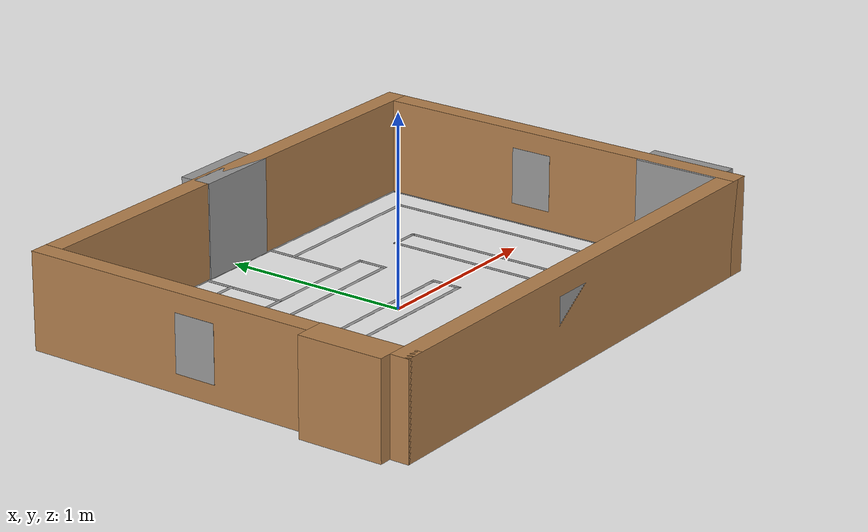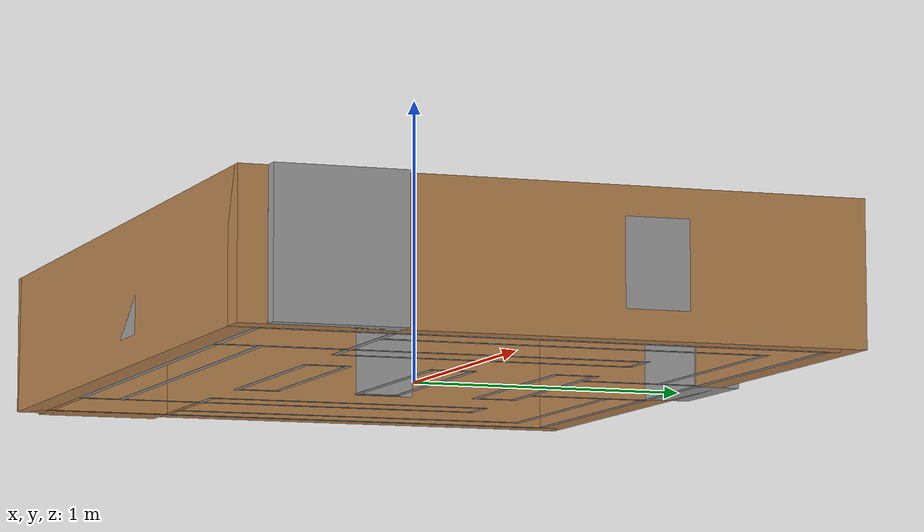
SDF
<?xml version='1.0'?>
<sdf version='1.6'>
  <model name='Map_2.0_0'>
    <link name='Door_2'>
      <pose frame=''>-1.38 -0.75 0 0 0 -1.56849</pose>
      <inertial>
        <mass>1</mass>
        <pose frame=''>0 0 0 0 -0 0</pose>
        <inertia>
          <ixx>1</ixx>
          <ixy>0</ixy>
          <ixz>0</ixz>
          <iyy>1</iyy>
          <iyz>0</iyz>
          <izz>1</izz>
        </inertia>
      </inertial>
      <self_collide>0</self_collide>
      <kinematic>0</kinematic>
      <visual name='Door_2_Visual'>
        <pose frame=''>0 0 0.25 0 -0 0</pose>
        <geometry>
          <box>
            <size>0.45 0.17 0.5</size>
          </box>
        </geometry>
        <material>
          <script>
            <uri>file://media/materials/scripts/gazebo.material</uri>
            <name>Gazebo/Wood</name>
          </script>
          <shader type='pixel'>
            <normal_map>__default__</normal_map>
          </shader>
          <ambient>0 0 0 1</ambient>
          <diffuse>0.7 0.7 0.7 1</diffuse>
          <specular>0.01 0.01 0.01 1</specular>
          <emissive>0 0 0 1</emissive>
        </material>
        <transparency>0</transparency>
        <cast_shadows>1</cast_shadows>
      </visual>
      <collision name='Door_2_Collision'>
        <laser_retro>0</laser_retro>
        <max_contacts>10</max_contacts>
        <pose frame=''>0 0 0.25 0 -0 0</pose>
        <geometry>
          <box>
            <size>0.45 0.17 0.5</size>
          </box>
        </geometry>
        <surface>
          <friction>
            <ode>
              <mu>1</mu>
              <mu2>1</mu2>
              <fdir1>0 0 0</fdir1>
              <slip1>0</slip1>
              <slip2>0</slip2>
            </ode>
            <torsional>
              <coefficient>1</coefficient>
              <patch_radius>0</patch_radius>
              <surface_radius>0</surface_radius>
              <use_patch_radius>1</use_patch_radius>
              <ode>
                <slip>0</slip>
              </ode>
            </torsional>
          </friction>
          <bounce>
            <restitution_coefficient>0</restitution_coefficient>
            <threshold>1e+06</threshold>
          </bounce>
          <contact>
            <collide_without_contact>0</collide_without_contact>
            <collide_without_contact_bitmask>1</collide_without_contact_bitmask>
            <collide_bitmask>1</collide_bitmask>
            <ode>
              <soft_cfm>0</soft_cfm>
              <soft_erp>0.2</soft_erp>
              <kp>1e+13</kp>
              <kd>1</kd>
              <max_vel>0.01</max_vel>
              <min_depth>0</min_depth>
            </ode>
            <bullet>
              <split_impulse>1</split_impulse>
              <split_impulse_penetration_threshold>-0.01</split_impulse_penetration_threshold>
              <soft_cfm>0</soft_cfm>
              <soft_erp>0.2</soft_erp>
              <kp>1e+13</kp>
              <kd>1</kd>
            </bullet>
          </contact>
        </surface>
      </collision>
    </link>
    <link name='Door_4'>
      <pose frame=''>1.37 -0.75 0 0 -0 1.57314</pose>
      <self_collide>0</self_collide>
      <kinematic>0</kinematic>
      <visual name='Door_4_Visual'>
        <pose frame=''>0 0 0.25 0 -0 0</pose>
        <geometry>
          <box>
            <size>0.45 0.17 0.5</size>
          </box>
        </geometry>
        <material>
          <script>
            <uri>file://media/materials/scripts/gazebo.material</uri>
            <name>Gazebo/Grey</name>
          </script>
          <shader type='pixel'/>
          <ambient>0.3 0.3 0.3 1</ambient>
          <diffuse>0.7 0.7 0.7 1</diffuse>
          <specular>0.01 0.01 0.01 1</specular>
          <emissive>0 0 0 1</emissive>
        </material>
        <transparency>0</transparency>
        <cast_shadows>1</cast_shadows>
      </visual>
      <collision name='Door_4_Collision'>
        <laser_retro>0</laser_retro>
        <max_contacts>10</max_contacts>
        <pose frame=''>0 0 0.25 0 -0 0</pose>
        <geometry>
          <box>
            <size>0.45 0.17 0.5</size>
          </box>
        </geometry>
        <surface>
          <friction>
            <ode>
              <mu>1</mu>
              <mu2>1</mu2>
              <fdir1>0 0 0</fdir1>
              <slip1>0</slip1>
              <slip2>0</slip2>
            </ode>
            <torsional>
              <coefficient>1</coefficient>
              <patch_radius>0</patch_radius>
              <surface_radius>0</surface_radius>
              <use_patch_radius>1</use_patch_radius>
              <ode>
                <slip>0</slip>
              </ode>
            </torsional>
          </friction>
          <bounce>
            <restitution_coefficient>0</restitution_coefficient>
            <threshold>1e+06</threshold>
          </bounce>
          <contact>
            <collide_without_contact>0</collide_without_contact>
            <collide_without_contact_bitmask>1</collide_without_contact_bitmask>
            <collide_bitmask>1</collide_bitmask>
            <ode>
              <soft_cfm>0</soft_cfm>
              <soft_erp>0.2</soft_erp>
              <kp>1e+13</kp>
              <kd>1</kd>
              <max_vel>0.01</max_vel>
              <min_depth>0</min_depth>
            </ode>
            <bullet>
              <split_impulse>1</split_impulse>
              <split_impulse_penetration_threshold>-0.01</split_impulse_penetration_threshold>
              <soft_cfm>0</soft_cfm>
              <soft_erp>0.2</soft_erp>
              <kp>1e+13</kp>
              <kd>1</kd>
            </bullet>
          </contact>
        </surface>
      </collision>
    </link>
    <link name='Door_5'>
      <pose frame=''>-0.005 1.055 0 0 0 -3.13908</pose>
      <self_collide>0</self_collide>
      <kinematic>0</kinematic>
      <visual name='Door_5_Visual'>
        <pose frame=''>0 0 0.25 0 -0 0</pose>
        <geometry>
          <box>
            <size>0.45 0.17 0.5</size>
          </box>
        </geometry>
        <material>
          <script>
            <uri>file://media/materials/scripts/gazebo.material</uri>
            <name>Gazebo/Grey</name>
          </script>
          <shader type='pixel'/>
          <ambient>0.3 0.3 0.3 1</ambient>
          <diffuse>0.7 0.7 0.7 1</diffuse>
          <specular>0.01 0.01 0.01 1</specular>
          <emissive>0 0 0 1</emissive>
        </material>
        <transparency>0</transparency>
        <cast_shadows>1</cast_shadows>
      </visual>
      <collision name='Door_5_Collision'>
        <laser_retro>0</laser_retro>
        <max_contacts>10</max_contacts>
        <pose frame=''>0 0 0.25 0 -0 0</pose>
        <geometry>
          <box>
            <size>0.45 0.17 0.5</size>
          </box>
        </geometry>
        <surface>
          <friction>
            <ode>
              <mu>1</mu>
              <mu2>1</mu2>
              <fdir1>0 0 0</fdir1>
              <slip1>0</slip1>
              <slip2>0</slip2>
            </ode>
            <torsional>
              <coefficient>1</coefficient>
              <patch_radius>0</patch_radius>
              <surface_radius>0</surface_radius>
              <use_patch_radius>1</use_patch_radius>
              <ode>
                <slip>0</slip>
              </ode>
            </torsional>
          </friction>
          <bounce>
            <restitution_coefficient>0</restitution_coefficient>
            <threshold>1e+06</threshold>
          </bounce>
          <contact>
            <collide_without_contact>0</collide_without_contact>
            <collide_without_contact_bitmask>1</collide_without_contact_bitmask>
            <collide_bitmask>1</collide_bitmask>
            <ode>
              <soft_cfm>0</soft_cfm>
              <soft_erp>0.2</soft_erp>
              <kp>1e+13</kp>
              <kd>1</kd>
              <max_vel>0.01</max_vel>
              <min_depth>0</min_depth>
            </ode>
            <bullet>
              <split_impulse>1</split_impulse>
              <split_impulse_penetration_threshold>-0.01</split_impulse_penetration_threshold>
              <soft_cfm>0</soft_cfm>
              <soft_erp>0.2</soft_erp>
              <kp>1e+13</kp>
              <kd>1</kd>
            </bullet>
          </contact>
        </surface>
      </collision>
    </link>
    <link name='Wall_0'>
      <pose frame=''>-1.075 -0.975 0 0 -0 0</pose>
      <self_collide>0</self_collide>
      <kinematic>0</kinematic>
      <visual name='Wall_0_Visual'>
        <pose frame=''>0 0 0 0 -0 0</pose>
        <geometry>
          <box>
            <size>0.47 0.02 0.001</size>
          </box>
        </geometry>
        <material>
          <script>
            <uri>file://media/materials/scripts/gazebo.material</uri>
            <name>Gazebo/Wood</name>
          </script>
          <ambient>1 0.835294 0 1</ambient>
          <shader type='pixel'/>
          <diffuse>1 1 1 1</diffuse>
          <specular>0.2 0.2 0.2 1</specular>
          <emissive>0 0 0 1</emissive>
        </material>
        <meta>
          <layer>0</layer>
        </meta>
        <transparency>0</transparency>
        <cast_shadows>1</cast_shadows>
      </visual>
      <collision name='Wall_0_Collision'>
        <laser_retro>0</laser_retro>
        <max_contacts>10</max_contacts>
        <pose frame=''>0 0 0 0 -0 0</pose>
        <geometry>
          <box>
            <size>0.47 0.02 0.001</size>
          </box>
        </geometry>
        <surface>
          <friction>
            <ode>
              <mu>1</mu>
              <mu2>1</mu2>
              <fdir1>0 0 0</fdir1>
              <slip1>0</slip1>
              <slip2>0</slip2>
            </ode>
            <torsional>
              <coefficient>1</coefficient>
              <patch_radius>0</patch_radius>
              <surface_radius>0</surface_radius>
              <use_patch_radius>1</use_patch_radius>
              <ode>
                <slip>0</slip>
              </ode>
            </torsional>
          </friction>
          <bounce>
            <restitution_coefficient>0</restitution_coefficient>
            <threshold>1e+06</threshold>
          </bounce>
          <contact>
            <collide_without_contact>0</collide_without_contact>
            <collide_without_contact_bitmask>1</collide_without_contact_bitmask>
            <collide_bitmask>1</collide_bitmask>
            <ode>
              <soft_cfm>0</soft_cfm>
              <soft_erp>0.2</soft_erp>
              <kp>1e+13</kp>
              <kd>1</kd>
              <max_vel>0.01</max_vel>
              <min_depth>0</min_depth>
            </ode>
            <bullet>
              <split_impulse>1</split_impulse>
              <split_impulse_penetration_threshold>-0.01</split_impulse_penetration_threshold>
              <soft_cfm>0</soft_cfm>
              <soft_erp>0.2</soft_erp>
              <kp>1e+13</kp>
              <kd>1</kd>
            </bullet>
          </contact>
        </surface>
      </collision>
    </link>
    <link name='Wall_15'>
      <pose frame=''>-1.15 0.15 0 0 -0 1.5708</pose>
      <self_collide>0</self_collide>
      <kinematic>0</kinematic>
      <visual name='Wall_15_Visual'>
        <pose frame=''>0 0 0 0 -0 0</pose>
        <geometry>
          <box>
            <size>1.37 0.02 0.001</size>
          </box>
        </geometry>
        <material>
          <script>
            <uri>file://media/materials/scripts/gazebo.material</uri>
            <name>Gazebo/Grey</name>
          </script>
          <ambient>1 1 1 1</ambient>
          <shader type='pixel'/>
          <diffuse>0.7 0.7 0.7 1</diffuse>
          <specular>0.01 0.01 0.01 1</specular>
          <emissive>0 0 0 1</emissive>
        </material>
        <meta>
          <layer>0</layer>
        </meta>
        <transparency>0</transparency>
        <cast_shadows>1</cast_shadows>
      </visual>
      <collision name='Wall_15_Collision'>
        <laser_retro>0</laser_retro>
        <max_contacts>10</max_contacts>
        <pose frame=''>0 0 0 0 -0 0</pose>
        <geometry>
          <box>
            <size>1.37 0.02 0.001</size>
          </box>
        </geometry>
        <surface>
          <friction>
            <ode>
              <mu>1</mu>
              <mu2>1</mu2>
              <fdir1>0 0 0</fdir1>
              <slip1>0</slip1>
              <slip2>0</slip2>
            </ode>
            <torsional>
              <coefficient>1</coefficient>
              <patch_radius>0</patch_radius>
              <surface_radius>0</surface_radius>
              <use_patch_radius>1</use_patch_radius>
              <ode>
                <slip>0</slip>
              </ode>
            </torsional>
          </friction>
          <bounce>
            <restitution_coefficient>0</restitution_coefficient>
            <threshold>1e+06</threshold>
          </bounce>
          <contact>
            <collide_without_contact>0</collide_without_contact>
            <collide_without_contact_bitmask>1</collide_without_contact_bitmask>
            <collide_bitmask>1</collide_bitmask>
            <ode>
              <soft_cfm>0</soft_cfm>
              <soft_erp>0.2</soft_erp>
              <kp>1e+13</kp>
              <kd>1</kd>
              <max_vel>0.01</max_vel>
              <min_depth>0</min_depth>
            </ode>
            <bullet>
              <split_impulse>1</split_impulse>
              <split_impulse_penetration_threshold>-0.01</split_impulse_penetration_threshold>
              <soft_cfm>0</soft_cfm>
              <soft_erp>0.2</soft_erp>
              <kp>1e+13</kp>
              <kd>1</kd>
            </bullet>
          </contact>
        </surface>
      </collision>
    </link>
    <link name='Wall_19'>
      <pose frame=''>-0.85 0 0 0 -0 1.5708</pose>
      <self_collide>0</self_collide>
      <kinematic>0</kinematic>
      <visual name='Wall_19_Visual'>
        <pose frame=''>0 0 0 0 -0 0</pose>
        <geometry>
          <box>
            <size>1.07 0.02 0.001</size>
          </box>
        </geometry>
        <material>
          <script>
            <uri>file://media/materials/scripts/gazebo.material</uri>
            <name>Gazebo/Grey</name>
          </script>
          <ambient>1 1 1 1</ambient>
          <shader type='pixel'/>
          <diffuse>0.7 0.7 0.7 1</diffuse>
          <specular>0.01 0.01 0.01 1</specular>
          <emissive>0 0 0 1</emissive>
        </material>
        <meta>
          <layer>0</layer>
        </meta>
        <transparency>0</transparency>
        <cast_shadows>1</cast_shadows>
      </visual>
      <collision name='Wall_19_Collision'>
        <laser_retro>0</laser_retro>
        <max_contacts>10</max_contacts>
        <pose frame=''>0 0 0 0 -0 0</pose>
        <geometry>
          <box>
            <size>1.07 0.02 0.001</size>
          </box>
        </geometry>
        <surface>
          <friction>
            <ode>
              <mu>1</mu>
              <mu2>1</mu2>
              <fdir1>0 0 0</fdir1>
              <slip1>0</slip1>
              <slip2>0</slip2>
            </ode>
            <torsional>
              <coefficient>1</coefficient>
              <patch_radius>0</patch_radius>
              <surface_radius>0</surface_radius>
              <use_patch_radius>1</use_patch_radius>
              <ode>
                <slip>0</slip>
              </ode>
            </torsional>
          </friction>
          <bounce>
            <restitution_coefficient>0</restitution_coefficient>
            <threshold>1e+06</threshold>
          </bounce>
          <contact>
            <collide_without_contact>0</collide_without_contact>
            <collide_without_contact_bitmask>1</collide_without_contact_bitmask>
            <collide_bitmask>1</collide_bitmask>
            <ode>
              <soft_cfm>0</soft_cfm>
              <soft_erp>0.2</soft_erp>
              <kp>1e+13</kp>
              <kd>1</kd>
              <max_vel>0.01</max_vel>
              <min_depth>0</min_depth>
            </ode>
            <bullet>
              <split_impulse>1</split_impulse>
              <split_impulse_penetration_threshold>-0.01</split_impulse_penetration_threshold>
              <soft_cfm>0</soft_cfm>
              <soft_erp>0.2</soft_erp>
              <kp>1e+13</kp>
              <kd>1</kd>
            </bullet>
          </contact>
        </surface>
      </collision>
    </link>
    <link name='Wall_2'>
      <pose frame=''>-0.85 -0.75 0 0 -0 1.5708</pose>
      <self_collide>0</self_collide>
      <kinematic>0</kinematic>
      <visual name='Wall_2_Visual'>
        <pose frame=''>0 0 0 0 -0 0</pose>
        <geometry>
          <box>
            <size>0.47 0.02 0.001</size>
          </box>
        </geometry>
        <material>
          <script>
            <uri>file://media/materials/scripts/gazebo.material</uri>
            <name>Gazebo/Grey</name>
          </script>
          <ambient>1 1 1 1</ambient>
          <shader type='pixel'/>
          <diffuse>0.7 0.7 0.7 1</diffuse>
          <specular>0.01 0.01 0.01 1</specular>
          <emissive>0 0 0 1</emissive>
        </material>
        <meta>
          <layer>0</layer>
        </meta>
        <transparency>0</transparency>
        <cast_shadows>1</cast_shadows>
      </visual>
      <collision name='Wall_2_Collision'>
        <laser_retro>0</laser_retro>
        <max_contacts>10</max_contacts>
        <pose frame=''>0 0 0 0 -0 0</pose>
        <geometry>
          <box>
            <size>0.47 0.02 0.001</size>
          </box>
        </geometry>
        <surface>
          <friction>
            <ode>
              <mu>1</mu>
              <mu2>1</mu2>
              <fdir1>0 0 0</fdir1>
              <slip1>0</slip1>
              <slip2>0</slip2>
            </ode>
            <torsional>
              <coefficient>1</coefficient>
              <patch_radius>0</patch_radius>
              <surface_radius>0</surface_radius>
              <use_patch_radius>1</use_patch_radius>
              <ode>
                <slip>0</slip>
              </ode>
            </torsional>
          </friction>
          <bounce>
            <restitution_coefficient>0</restitution_coefficient>
            <threshold>1e+06</threshold>
          </bounce>
          <contact>
            <collide_without_contact>0</collide_without_contact>
            <collide_without_contact_bitmask>1</collide_without_contact_bitmask>
            <collide_bitmask>1</collide_bitmask>
            <ode>
              <soft_cfm>0</soft_cfm>
              <soft_erp>0.2</soft_erp>
              <kp>1e+13</kp>
              <kd>1</kd>
              <max_vel>0.01</max_vel>
              <min_depth>0</min_depth>
            </ode>
            <bullet>
              <split_impulse>1</split_impulse>
              <split_impulse_penetration_threshold>-0.01</split_impulse_penetration_threshold>
              <soft_cfm>0</soft_cfm>
              <soft_erp>0.2</soft_erp>
              <kp>1e+13</kp>
              <kd>1</kd>
            </bullet>
          </contact>
        </surface>
      </collision>
    </link>
    <link name='Wall_21'>
      <pose frame=''>-0.775 -0.525 0 0 -0 0</pose>
      <self_collide>0</self_collide>
      <kinematic>0</kinematic>
      <visual name='Wall_21_Visual'>
        <pose frame=''>0 0 0 0 -0 0</pose>
        <geometry>
          <box>
            <size>0.17 0.02 0.001</size>
          </box>
        </geometry>
        <material>
          <script>
            <uri>file://media/materials/scripts/gazebo.material</uri>
            <name>Gazebo/Grey</name>
          </script>
          <ambient>1 1 1 1</ambient>
          <shader type='pixel'/>
          <diffuse>0.7 0.7 0.7 1</diffuse>
          <specular>0.01 0.01 0.01 1</specular>
          <emissive>0 0 0 1</emissive>
        </material>
        <meta>
          <layer>0</layer>
        </meta>
        <transparency>0</transparency>
        <cast_shadows>1</cast_shadows>
      </visual>
      <collision name='Wall_21_Collision'>
        <laser_retro>0</laser_retro>
        <max_contacts>10</max_contacts>
        <pose frame=''>0 0 0 0 -0 0</pose>
        <geometry>
          <box>
            <size>0.17 0.02 0.001</size>
          </box>
        </geometry>
        <surface>
          <friction>
            <ode>
              <mu>1</mu>
              <mu2>1</mu2>
              <fdir1>0 0 0</fdir1>
              <slip1>0</slip1>
              <slip2>0</slip2>
            </ode>
            <torsional>
              <coefficient>1</coefficient>
              <patch_radius>0</patch_radius>
              <surface_radius>0</surface_radius>
              <use_patch_radius>1</use_patch_radius>
              <ode>
                <slip>0</slip>
              </ode>
            </torsional>
          </friction>
          <bounce>
            <restitution_coefficient>0</restitution_coefficient>
            <threshold>1e+06</threshold>
          </bounce>
          <contact>
            <collide_without_contact>0</collide_without_contact>
            <collide_without_contact_bitmask>1</collide_without_contact_bitmask>
            <collide_bitmask>1</collide_bitmask>
            <ode>
              <soft_cfm>0</soft_cfm>
              <soft_erp>0.2</soft_erp>
              <kp>1e+13</kp>
              <kd>1</kd>
              <max_vel>0.01</max_vel>
              <min_depth>0</min_depth>
            </ode>
            <bullet>
              <split_impulse>1</split_impulse>
              <split_impulse_penetration_threshold>-0.01</split_impulse_penetration_threshold>
              <soft_cfm>0</soft_cfm>
              <soft_erp>0.2</soft_erp>
              <kp>1e+13</kp>
              <kd>1</kd>
            </bullet>
          </contact>
        </surface>
      </collision>
    </link>
    <link name='Wall_23'>
      <pose frame=''>-0.7 0 0 0 -0 1.5708</pose>
      <self_collide>0</self_collide>
      <kinematic>0</kinematic>
      <visual name='Wall_23_Visual'>
        <pose frame=''>0 0 0 0 -0 0</pose>
        <geometry>
          <box>
            <size>1.07 0.02 0.001</size>
          </box>
        </geometry>
        <material>
          <script>
            <uri>file://media/materials/scripts/gazebo.material</uri>
            <name>Gazebo/Grey</name>
          </script>
          <ambient>1 1 1 1</ambient>
          <shader type='pixel'/>
          <diffuse>0.7 0.7 0.7 1</diffuse>
          <specular>0.01 0.01 0.01 1</specular>
          <emissive>0 0 0 1</emissive>
        </material>
        <meta>
          <layer>0</layer>
        </meta>
        <transparency>0</transparency>
        <cast_shadows>1</cast_shadows>
      </visual>
      <collision name='Wall_23_Collision'>
        <laser_retro>0</laser_retro>
        <max_contacts>10</max_contacts>
        <pose frame=''>0 0 0 0 -0 0</pose>
        <geometry>
          <box>
            <size>1.07 0.02 0.001</size>
          </box>
        </geometry>
        <surface>
          <friction>
            <ode>
              <mu>1</mu>
              <mu2>1</mu2>
              <fdir1>0 0 0</fdir1>
              <slip1>0</slip1>
              <slip2>0</slip2>
            </ode>
            <torsional>
              <coefficient>1</coefficient>
              <patch_radius>0</patch_radius>
              <surface_radius>0</surface_radius>
              <use_patch_radius>1</use_patch_radius>
              <ode>
                <slip>0</slip>
              </ode>
            </torsional>
          </friction>
          <bounce>
            <restitution_coefficient>0</restitution_coefficient>
            <threshold>1e+06</threshold>
          </bounce>
          <contact>
            <collide_without_contact>0</collide_without_contact>
            <collide_without_contact_bitmask>1</collide_without_contact_bitmask>
            <collide_bitmask>1</collide_bitmask>
            <ode>
              <soft_cfm>0</soft_cfm>
              <soft_erp>0.2</soft_erp>
              <kp>1e+13</kp>
              <kd>1</kd>
              <max_vel>0.01</max_vel>
              <min_depth>0</min_depth>
            </ode>
            <bullet>
              <split_impulse>1</split_impulse>
              <split_impulse_penetration_threshold>-0.01</split_impulse_penetration_threshold>
              <soft_cfm>0</soft_cfm>
              <soft_erp>0.2</soft_erp>
              <kp>1e+13</kp>
              <kd>1</kd>
            </bullet>
          </contact>
        </surface>
      </collision>
    </link>
    <link name='Wall_25'>
      <pose frame=''>0 -0.825 0 0 -0 0</pose>
      <self_collide>0</self_collide>
      <kinematic>0</kinematic>
      <visual name='Wall_25_Visual'>
        <pose frame=''>0 0 0 0 -0 0</pose>
        <geometry>
          <box>
            <size>1.72 0.02 0.001</size>
          </box>
        </geometry>
        <material>
          <script>
            <uri>file://media/materials/scripts/gazebo.material</uri>
            <name>Gazebo/Grey</name>
          </script>
          <ambient>1 1 1 1</ambient>
          <shader type='pixel'/>
          <diffuse>0.7 0.7 0.7 1</diffuse>
          <specular>0.01 0.01 0.01 1</specular>
          <emissive>0 0 0 1</emissive>
        </material>
        <meta>
          <layer>0</layer>
        </meta>
        <transparency>0</transparency>
        <cast_shadows>1</cast_shadows>
      </visual>
      <collision name='Wall_25_Collision'>
        <laser_retro>0</laser_retro>
        <max_contacts>10</max_contacts>
        <pose frame=''>0 0 0 0 -0 0</pose>
        <geometry>
          <box>
            <size>1.72 0.02 0.001</size>
          </box>
        </geometry>
        <surface>
          <friction>
            <ode>
              <mu>1</mu>
              <mu2>1</mu2>
              <fdir1>0 0 0</fdir1>
              <slip1>0</slip1>
              <slip2>0</slip2>
            </ode>
            <torsional>
              <coefficient>1</coefficient>
              <patch_radius>0</patch_radius>
              <surface_radius>0</surface_radius>
              <use_patch_radius>1</use_patch_radius>
              <ode>
                <slip>0</slip>
              </ode>
            </torsional>
          </friction>
          <bounce>
            <restitution_coefficient>0</restitution_coefficient>
            <threshold>1e+06</threshold>
          </bounce>
          <contact>
            <collide_without_contact>0</collide_without_contact>
            <collide_without_contact_bitmask>1</collide_without_contact_bitmask>
            <collide_bitmask>1</collide_bitmask>
            <ode>
              <soft_cfm>0</soft_cfm>
              <soft_erp>0.2</soft_erp>
              <kp>1e+13</kp>
              <kd>1</kd>
              <max_vel>0.01</max_vel>
              <min_depth>0</min_depth>
            </ode>
            <bullet>
              <split_impulse>1</split_impulse>
              <split_impulse_penetration_threshold>-0.01</split_impulse_penetration_threshold>
              <soft_cfm>0</soft_cfm>
              <soft_erp>0.2</soft_erp>
              <kp>1e+13</kp>
              <kd>1</kd>
            </bullet>
          </contact>
        </surface>
      </collision>
    </link>
    <link name='Wall_27'>
      <pose frame=''>0.225 -0.975 0 0 -0 0</pose>
      <self_collide>0</self_collide>
      <kinematic>0</kinematic>
      <visual name='Wall_27_Visual'>
        <pose frame=''>0 0 0 0 -0 0</pose>
        <geometry>
          <box>
            <size>2.17 0.02 0.001</size>
          </box>
        </geometry>
        <material>
          <script>
            <uri>file://media/materials/scripts/gazebo.material</uri>
            <name>Gazebo/Grey</name>
          </script>
          <ambient>1 1 1 1</ambient>
          <shader type='pixel'/>
          <diffuse>0.7 0.7 0.7 1</diffuse>
          <specular>0.01 0.01 0.01 1</specular>
          <emissive>0 0 0 1</emissive>
        </material>
        <meta>
          <layer>0</layer>
        </meta>
        <transparency>0</transparency>
        <cast_shadows>1</cast_shadows>
      </visual>
      <collision name='Wall_27_Collision'>
        <laser_retro>0</laser_retro>
        <max_contacts>10</max_contacts>
        <pose frame=''>0 0 0 0 -0 0</pose>
        <geometry>
          <box>
            <size>2.17 0.02 0.001</size>
          </box>
        </geometry>
        <surface>
          <friction>
            <ode>
              <mu>1</mu>
              <mu2>1</mu2>
              <fdir1>0 0 0</fdir1>
              <slip1>0</slip1>
              <slip2>0</slip2>
            </ode>
            <torsional>
              <coefficient>1</coefficient>
              <patch_radius>0</patch_radius>
              <surface_radius>0</surface_radius>
              <use_patch_radius>1</use_patch_radius>
              <ode>
                <slip>0</slip>
              </ode>
            </torsional>
          </friction>
          <bounce>
            <restitution_coefficient>0</restitution_coefficient>
            <threshold>1e+06</threshold>
          </bounce>
          <contact>
            <collide_without_contact>0</collide_without_contact>
            <collide_without_contact_bitmask>1</collide_without_contact_bitmask>
            <collide_bitmask>1</collide_bitmask>
            <ode>
              <soft_cfm>0</soft_cfm>
              <soft_erp>0.2</soft_erp>
              <kp>1e+13</kp>
              <kd>1</kd>
              <max_vel>0.01</max_vel>
              <min_depth>0</min_depth>
            </ode>
            <bullet>
              <split_impulse>1</split_impulse>
              <split_impulse_penetration_threshold>-0.01</split_impulse_penetration_threshold>
              <soft_cfm>0</soft_cfm>
              <soft_erp>0.2</soft_erp>
              <kp>1e+13</kp>
              <kd>1</kd>
            </bullet>
          </contact>
        </surface>
      </collision>
    </link>
    <link name='Wall_29'>
      <pose frame=''>0 0.975 0 0 -0 0</pose>
      <self_collide>0</self_collide>
      <kinematic>0</kinematic>
      <visual name='Wall_29_Visual'>
        <pose frame=''>0 0 0 0 -0 0</pose>
        <geometry>
          <box>
            <size>2.62 0.02 0.001</size>
          </box>
        </geometry>
        <material>
          <script>
            <uri>file://media/materials/scripts/gazebo.material</uri>
            <name>Gazebo/Grey</name>
          </script>
          <ambient>1 1 1 1</ambient>
          <shader type='pixel'/>
          <diffuse>0.7 0.7 0.7 1</diffuse>
          <specular>0.01 0.01 0.01 1</specular>
          <emissive>0 0 0 1</emissive>
        </material>
        <meta>
          <layer>0</layer>
        </meta>
        <transparency>0</transparency>
        <cast_shadows>1</cast_shadows>
      </visual>
      <collision name='Wall_29_Collision'>
        <laser_retro>0</laser_retro>
        <max_contacts>10</max_contacts>
        <pose frame=''>0 0 0 0 -0 0</pose>
        <geometry>
          <box>
            <size>2.62 0.02 0.001</size>
          </box>
        </geometry>
        <surface>
          <friction>
            <ode>
              <mu>1</mu>
              <mu2>1</mu2>
              <fdir1>0 0 0</fdir1>
              <slip1>0</slip1>
              <slip2>0</slip2>
            </ode>
            <torsional>
              <coefficient>1</coefficient>
              <patch_radius>0</patch_radius>
              <surface_radius>0</surface_radius>
              <use_patch_radius>1</use_patch_radius>
              <ode>
                <slip>0</slip>
              </ode>
            </torsional>
          </friction>
          <bounce>
            <restitution_coefficient>0</restitution_coefficient>
            <threshold>1e+06</threshold>
          </bounce>
          <contact>
            <collide_without_contact>0</collide_without_contact>
            <collide_without_contact_bitmask>1</collide_without_contact_bitmask>
            <collide_bitmask>1</collide_bitmask>
            <ode>
              <soft_cfm>0</soft_cfm>
              <soft_erp>0.2</soft_erp>
              <kp>1e+13</kp>
              <kd>1</kd>
              <max_vel>0.01</max_vel>
              <min_depth>0</min_depth>
            </ode>
            <bullet>
              <split_impulse>1</split_impulse>
              <split_impulse_penetration_threshold>-0.01</split_impulse_penetration_threshold>
              <soft_cfm>0</soft_cfm>
              <soft_erp>0.2</soft_erp>
              <kp>1e+13</kp>
              <kd>1</kd>
            </bullet>
          </contact>
        </surface>
      </collision>
    </link>
    <link name='Wall_31'>
      <pose frame=''>-0.7 0.825 0 0 -0 0</pose>
      <self_collide>0</self_collide>
      <kinematic>0</kinematic>
      <visual name='Wall_31_Visual'>
        <pose frame=''>0 0 0 0 -0 0</pose>
        <geometry>
          <box>
            <size>0.92 0.02 0.001</size>
          </box>
        </geometry>
        <material>
          <script>
            <uri>file://media/materials/scripts/gazebo.material</uri>
            <name>Gazebo/Grey</name>
          </script>
          <ambient>1 1 1 1</ambient>
          <shader type='pixel'/>
          <diffuse>0.7 0.7 0.7 1</diffuse>
          <specular>0.01 0.01 0.01 1</specular>
          <emissive>0 0 0 1</emissive>
        </material>
        <meta>
          <layer>0</layer>
        </meta>
        <transparency>0</transparency>
        <cast_shadows>1</cast_shadows>
      </visual>
      <collision name='Wall_31_Collision'>
        <laser_retro>0</laser_retro>
        <max_contacts>10</max_contacts>
        <pose frame=''>0 0 0 0 -0 0</pose>
        <geometry>
          <box>
            <size>0.92 0.02 0.001</size>
          </box>
        </geometry>
        <surface>
          <friction>
            <ode>
              <mu>1</mu>
              <mu2>1</mu2>
              <fdir1>0 0 0</fdir1>
              <slip1>0</slip1>
              <slip2>0</slip2>
            </ode>
            <torsional>
              <coefficient>1</coefficient>
              <patch_radius>0</patch_radius>
              <surface_radius>0</surface_radius>
              <use_patch_radius>1</use_patch_radius>
              <ode>
                <slip>0</slip>
              </ode>
            </torsional>
          </friction>
          <bounce>
            <restitution_coefficient>0</restitution_coefficient>
            <threshold>1e+06</threshold>
          </bounce>
          <contact>
            <collide_without_contact>0</collide_without_contact>
            <collide_without_contact_bitmask>1</collide_without_contact_bitmask>
            <collide_bitmask>1</collide_bitmask>
            <ode>
              <soft_cfm>0</soft_cfm>
              <soft_erp>0.2</soft_erp>
              <kp>1e+13</kp>
              <kd>1</kd>
              <max_vel>0.01</max_vel>
              <min_depth>0</min_depth>
            </ode>
            <bullet>
              <split_impulse>1</split_impulse>
              <split_impulse_penetration_threshold>-0.01</split_impulse_penetration_threshold>
              <soft_cfm>0</soft_cfm>
              <soft_erp>0.2</soft_erp>
              <kp>1e+13</kp>
              <kd>1</kd>
            </bullet>
          </contact>
        </surface>
      </collision>
    </link>
    <link name='Wall_33'>
      <pose frame=''>-0.25 0.75 0 0 0 -1.5708</pose>
      <self_collide>0</self_collide>
      <kinematic>0</kinematic>
      <visual name='Wall_33_Visual'>
        <pose frame=''>0 0 0 0 -0 0</pose>
        <geometry>
          <box>
            <size>0.47 0.02 0.001</size>
          </box>
        </geometry>
        <material>
          <script>
            <uri>file://media/materials/scripts/gazebo.material</uri>
            <name>Gazebo/Grey</name>
          </script>
          <ambient>1 1 1 1</ambient>
          <shader type='pixel'/>
          <diffuse>0.7 0.7 0.7 1</diffuse>
          <specular>0.01 0.01 0.01 1</specular>
          <emissive>0 0 0 1</emissive>
        </material>
        <meta>
          <layer>0</layer>
        </meta>
        <transparency>0</transparency>
        <cast_shadows>1</cast_shadows>
      </visual>
      <collision name='Wall_33_Collision'>
        <laser_retro>0</laser_retro>
        <max_contacts>10</max_contacts>
        <pose frame=''>0 0 0 0 -0 0</pose>
        <geometry>
          <box>
            <size>0.47 0.02 0.001</size>
          </box>
        </geometry>
        <surface>
          <friction>
            <ode>
              <mu>1</mu>
              <mu2>1</mu2>
              <fdir1>0 0 0</fdir1>
              <slip1>0</slip1>
              <slip2>0</slip2>
            </ode>
            <torsional>
              <coefficient>1</coefficient>
              <patch_radius>0</patch_radius>
              <surface_radius>0</surface_radius>
              <use_patch_radius>1</use_patch_radius>
              <ode>
                <slip>0</slip>
              </ode>
            </torsional>
          </friction>
          <bounce>
            <restitution_coefficient>0</restitution_coefficient>
            <threshold>1e+06</threshold>
          </bounce>
          <contact>
            <collide_without_contact>0</collide_without_contact>
            <collide_without_contact_bitmask>1</collide_without_contact_bitmask>
            <collide_bitmask>1</collide_bitmask>
            <ode>
              <soft_cfm>0</soft_cfm>
              <soft_erp>0.2</soft_erp>
              <kp>1e+13</kp>
              <kd>1</kd>
              <max_vel>0.01</max_vel>
              <min_depth>0</min_depth>
            </ode>
            <bullet>
              <split_impulse>1</split_impulse>
              <split_impulse_penetration_threshold>-0.01</split_impulse_penetration_threshold>
              <soft_cfm>0</soft_cfm>
              <soft_erp>0.2</soft_erp>
              <kp>1e+13</kp>
              <kd>1</kd>
            </bullet>
          </contact>
        </surface>
      </collision>
    </link>
    <link name='Wall_35'>
      <pose frame=''>-0.775 0.525 0 0 -0 0</pose>
      <self_collide>0</self_collide>
      <kinematic>0</kinematic>
      <visual name='Wall_35_Visual'>
        <pose frame=''>0 0 0 0 -0 0</pose>
        <geometry>
          <box>
            <size>0.17 0.02 0.001</size>
          </box>
        </geometry>
        <material>
          <script>
            <uri>file://media/materials/scripts/gazebo.material</uri>
            <name>Gazebo/Grey</name>
          </script>
          <ambient>1 1 1 1</ambient>
          <shader type='pixel'/>
          <diffuse>0.7 0.7 0.7 1</diffuse>
          <specular>0.01 0.01 0.01 1</specular>
          <emissive>0 0 0 1</emissive>
        </material>
        <meta>
          <layer>0</layer>
        </meta>
        <transparency>0</transparency>
        <cast_shadows>1</cast_shadows>
      </visual>
      <collision name='Wall_35_Collision'>
        <laser_retro>0</laser_retro>
        <max_contacts>10</max_contacts>
        <pose frame=''>0 0 0 0 -0 0</pose>
        <geometry>
          <box>
            <size>0.17 0.02 0.001</size>
          </box>
        </geometry>
        <surface>
          <friction>
            <ode>
              <mu>1</mu>
              <mu2>1</mu2>
              <fdir1>0 0 0</fdir1>
              <slip1>0</slip1>
              <slip2>0</slip2>
            </ode>
            <torsional>
              <coefficient>1</coefficient>
              <patch_radius>0</patch_radius>
              <surface_radius>0</surface_radius>
              <use_patch_radius>1</use_patch_radius>
              <ode>
                <slip>0</slip>
              </ode>
            </torsional>
          </friction>
          <bounce>
            <restitution_coefficient>0</restitution_coefficient>
            <threshold>1e+06</threshold>
          </bounce>
          <contact>
            <collide_without_contact>0</collide_without_contact>
            <collide_without_contact_bitmask>1</collide_without_contact_bitmask>
            <collide_bitmask>1</collide_bitmask>
            <ode>
              <soft_cfm>0</soft_cfm>
              <soft_erp>0.2</soft_erp>
              <kp>1e+13</kp>
              <kd>1</kd>
              <max_vel>0.01</max_vel>
              <min_depth>0</min_depth>
            </ode>
            <bullet>
              <split_impulse>1</split_impulse>
              <split_impulse_penetration_threshold>-0.01</split_impulse_penetration_threshold>
              <soft_cfm>0</soft_cfm>
              <soft_erp>0.2</soft_erp>
              <kp>1e+13</kp>
              <kd>1</kd>
            </bullet>
          </contact>
        </surface>
      </collision>
    </link>
    <link name='Wall_37'>
      <pose frame=''>0 0.525 0 0 -0 0</pose>
      <self_collide>0</self_collide>
      <kinematic>0</kinematic>
      <visual name='Wall_37_Visual'>
        <pose frame=''>0 0 0 0 -0 0</pose>
        <geometry>
          <box>
            <size>0.82 0.02 0.001</size>
          </box>
        </geometry>
        <material>
          <script>
            <uri>file://media/materials/scripts/gazebo.material</uri>
            <name>Gazebo/Grey</name>
          </script>
          <ambient>1 1 1 1</ambient>
          <shader type='pixel'/>
          <diffuse>0.7 0.7 0.7 1</diffuse>
          <specular>0.01 0.01 0.01 1</specular>
          <emissive>0 0 0 1</emissive>
        </material>
        <meta>
          <layer>0</layer>
        </meta>
        <transparency>0</transparency>
        <cast_shadows>1</cast_shadows>
      </visual>
      <collision name='Wall_37_Collision'>
        <laser_retro>0</laser_retro>
        <max_contacts>10</max_contacts>
        <pose frame=''>0 0 0 0 -0 0</pose>
        <geometry>
          <box>
            <size>0.82 0.02 0.001</size>
          </box>
        </geometry>
        <surface>
          <friction>
            <ode>
              <mu>1</mu>
              <mu2>1</mu2>
              <fdir1>0 0 0</fdir1>
              <slip1>0</slip1>
              <slip2>0</slip2>
            </ode>
            <torsional>
              <coefficient>1</coefficient>
              <patch_radius>0</patch_radius>
              <surface_radius>0</surface_radius>
              <use_patch_radius>1</use_patch_radius>
              <ode>
                <slip>0</slip>
              </ode>
            </torsional>
          </friction>
          <bounce>
            <restitution_coefficient>0</restitution_coefficient>
            <threshold>1e+06</threshold>
          </bounce>
          <contact>
            <collide_without_contact>0</collide_without_contact>
            <collide_without_contact_bitmask>1</collide_without_contact_bitmask>
            <collide_bitmask>1</collide_bitmask>
            <ode>
              <soft_cfm>0</soft_cfm>
              <soft_erp>0.2</soft_erp>
              <kp>1e+13</kp>
              <kd>1</kd>
              <max_vel>0.01</max_vel>
              <min_depth>0</min_depth>
            </ode>
            <bullet>
              <split_impulse>1</split_impulse>
              <split_impulse_penetration_threshold>-0.01</split_impulse_penetration_threshold>
              <soft_cfm>0</soft_cfm>
              <soft_erp>0.2</soft_erp>
              <kp>1e+13</kp>
              <kd>1</kd>
            </bullet>
          </contact>
        </surface>
      </collision>
    </link>
    <link name='Wall_39'>
      <pose frame=''>0.4 0.45 0 0 0 -1.5708</pose>
      <self_collide>0</self_collide>
      <kinematic>0</kinematic>
      <visual name='Wall_39_Visual'>
        <pose frame=''>0 0 0 0 -0 0</pose>
        <geometry>
          <box>
            <size>0.17 0.02 0.001</size>
          </box>
        </geometry>
        <material>
          <script>
            <uri>file://media/materials/scripts/gazebo.material</uri>
            <name>Gazebo/Grey</name>
          </script>
          <ambient>1 1 1 1</ambient>
          <shader type='pixel'/>
          <diffuse>0.7 0.7 0.7 1</diffuse>
          <specular>0.01 0.01 0.01 1</specular>
          <emissive>0 0 0 1</emissive>
        </material>
        <meta>
          <layer>0</layer>
        </meta>
        <transparency>0</transparency>
        <cast_shadows>1</cast_shadows>
      </visual>
      <collision name='Wall_39_Collision'>
        <laser_retro>0</laser_retro>
        <max_contacts>10</max_contacts>
        <pose frame=''>0 0 0 0 -0 0</pose>
        <geometry>
          <box>
            <size>0.17 0.02 0.001</size>
          </box>
        </geometry>
        <surface>
          <friction>
            <ode>
              <mu>1</mu>
              <mu2>1</mu2>
              <fdir1>0 0 0</fdir1>
              <slip1>0</slip1>
              <slip2>0</slip2>
            </ode>
            <torsional>
              <coefficient>1</coefficient>
              <patch_radius>0</patch_radius>
              <surface_radius>0</surface_radius>
              <use_patch_radius>1</use_patch_radius>
              <ode>
                <slip>0</slip>
              </ode>
            </torsional>
          </friction>
          <bounce>
            <restitution_coefficient>0</restitution_coefficient>
            <threshold>1e+06</threshold>
          </bounce>
          <contact>
            <collide_without_contact>0</collide_without_contact>
            <collide_without_contact_bitmask>1</collide_without_contact_bitmask>
            <collide_bitmask>1</collide_bitmask>
            <ode>
              <soft_cfm>0</soft_cfm>
              <soft_erp>0.2</soft_erp>
              <kp>1e+13</kp>
              <kd>1</kd>
              <max_vel>0.01</max_vel>
              <min_depth>0</min_depth>
            </ode>
            <bullet>
              <split_impulse>1</split_impulse>
              <split_impulse_penetration_threshold>-0.01</split_impulse_penetration_threshold>
              <soft_cfm>0</soft_cfm>
              <soft_erp>0.2</soft_erp>
              <kp>1e+13</kp>
              <kd>1</kd>
            </bullet>
          </contact>
        </surface>
      </collision>
    </link>
    <link name='Wall_4'>
      <pose frame=''>-1.3 -0.75 0 0 -0 1.5708</pose>
      <self_collide>0</self_collide>
      <kinematic>0</kinematic>
      <visual name='Wall_4_Visual'>
        <pose frame=''>0 0 0 0 -0 0</pose>
        <geometry>
          <box>
            <size>0.47 0.02 0.001</size>
          </box>
        </geometry>
        <material>
          <script>
            <uri>file://media/materials/scripts/gazebo.material</uri>
            <name>Gazebo/Wood</name>
          </script>
          <ambient>1 0.764706 0.305882 1</ambient>
          <shader type='pixel'/>
          <diffuse>1 1 1 1</diffuse>
          <specular>0.2 0.2 0.2 1</specular>
          <emissive>0 0 0 1</emissive>
        </material>
        <meta>
          <layer>0</layer>
        </meta>
        <transparency>0</transparency>
        <cast_shadows>1</cast_shadows>
      </visual>
      <collision name='Wall_4_Collision'>
        <laser_retro>0</laser_retro>
        <max_contacts>10</max_contacts>
        <pose frame=''>0 0 0 0 -0 0</pose>
        <geometry>
          <box>
            <size>0.47 0.02 0.001</size>
          </box>
        </geometry>
        <surface>
          <friction>
            <ode>
              <mu>1</mu>
              <mu2>1</mu2>
              <fdir1>0 0 0</fdir1>
              <slip1>0</slip1>
              <slip2>0</slip2>
            </ode>
            <torsional>
              <coefficient>1</coefficient>
              <patch_radius>0</patch_radius>
              <surface_radius>0</surface_radius>
              <use_patch_radius>1</use_patch_radius>
              <ode>
                <slip>0</slip>
              </ode>
            </torsional>
          </friction>
          <bounce>
            <restitution_coefficient>0</restitution_coefficient>
            <threshold>1e+06</threshold>
          </bounce>
          <contact>
            <collide_without_contact>0</collide_without_contact>
            <collide_without_contact_bitmask>1</collide_without_contact_bitmask>
            <collide_bitmask>1</collide_bitmask>
            <ode>
              <soft_cfm>0</soft_cfm>
              <soft_erp>0.2</soft_erp>
              <kp>1e+13</kp>
              <kd>1</kd>
              <max_vel>0.01</max_vel>
              <min_depth>0</min_depth>
            </ode>
            <bullet>
              <split_impulse>1</split_impulse>
              <split_impulse_penetration_threshold>-0.01</split_impulse_penetration_threshold>
              <soft_cfm>0</soft_cfm>
              <soft_erp>0.2</soft_erp>
              <kp>1e+13</kp>
              <kd>1</kd>
            </bullet>
          </contact>
        </surface>
      </collision>
    </link>
    <link name='Wall_41'>
      <pose frame=''>0 0.075 0 0 -0 0</pose>
      <self_collide>0</self_collide>
      <kinematic>0</kinematic>
      <visual name='Wall_41_Visual'>
        <pose frame=''>0 0 0 0 -0 0</pose>
        <geometry>
          <box>
            <size>0.82 0.02 0.001</size>
          </box>
        </geometry>
        <material>
          <script>
            <uri>file://media/materials/scripts/gazebo.material</uri>
            <name>Gazebo/Grey</name>
          </script>
          <ambient>1 1 1 1</ambient>
          <shader type='pixel'/>
          <diffuse>0.7 0.7 0.7 1</diffuse>
          <specular>0.01 0.01 0.01 1</specular>
          <emissive>0 0 0 1</emissive>
        </material>
        <meta>
          <layer>0</layer>
        </meta>
        <transparency>0</transparency>
        <cast_shadows>1</cast_shadows>
      </visual>
      <collision name='Wall_41_Collision'>
        <laser_retro>0</laser_retro>
        <max_contacts>10</max_contacts>
        <pose frame=''>0 0 0 0 -0 0</pose>
        <geometry>
          <box>
            <size>0.82 0.02 0.001</size>
          </box>
        </geometry>
        <surface>
          <friction>
            <ode>
              <mu>1</mu>
              <mu2>1</mu2>
              <fdir1>0 0 0</fdir1>
              <slip1>0</slip1>
              <slip2>0</slip2>
            </ode>
            <torsional>
              <coefficient>1</coefficient>
              <patch_radius>0</patch_radius>
              <surface_radius>0</surface_radius>
              <use_patch_radius>1</use_patch_radius>
              <ode>
                <slip>0</slip>
              </ode>
            </torsional>
          </friction>
          <bounce>
            <restitution_coefficient>0</restitution_coefficient>
            <threshold>1e+06</threshold>
          </bounce>
          <contact>
            <collide_without_contact>0</collide_without_contact>
            <collide_without_contact_bitmask>1</collide_without_contact_bitmask>
            <collide_bitmask>1</collide_bitmask>
            <ode>
              <soft_cfm>0</soft_cfm>
              <soft_erp>0.2</soft_erp>
              <kp>1e+13</kp>
              <kd>1</kd>
              <max_vel>0.01</max_vel>
              <min_depth>0</min_depth>
            </ode>
            <bullet>
              <split_impulse>1</split_impulse>
              <split_impulse_penetration_threshold>-0.01</split_impulse_penetration_threshold>
              <soft_cfm>0</soft_cfm>
              <soft_erp>0.2</soft_erp>
              <kp>1e+13</kp>
              <kd>1</kd>
            </bullet>
          </contact>
        </surface>
      </collision>
    </link>
    <link name='Wall_43'>
      <pose frame=''>0 -0.075 0 0 -0 0</pose>
      <self_collide>0</self_collide>
      <kinematic>0</kinematic>
      <visual name='Wall_43_Visual'>
        <pose frame=''>0 0 0 0 -0 0</pose>
        <geometry>
          <box>
            <size>0.82 0.02 0.001</size>
          </box>
        </geometry>
        <material>
          <script>
            <uri>file://media/materials/scripts/gazebo.material</uri>
            <name>Gazebo/Grey</name>
          </script>
          <ambient>1 1 1 1</ambient>
          <shader type='pixel'/>
          <diffuse>0.7 0.7 0.7 1</diffuse>
          <specular>0.01 0.01 0.01 1</specular>
          <emissive>0 0 0 1</emissive>
        </material>
        <meta>
          <layer>0</layer>
        </meta>
        <transparency>0</transparency>
        <cast_shadows>1</cast_shadows>
      </visual>
      <collision name='Wall_43_Collision'>
        <laser_retro>0</laser_retro>
        <max_contacts>10</max_contacts>
        <pose frame=''>0 0 0 0 -0 0</pose>
        <geometry>
          <box>
            <size>0.82 0.02 0.001</size>
          </box>
        </geometry>
        <surface>
          <friction>
            <ode>
              <mu>1</mu>
              <mu2>1</mu2>
              <fdir1>0 0 0</fdir1>
              <slip1>0</slip1>
              <slip2>0</slip2>
            </ode>
            <torsional>
              <coefficient>1</coefficient>
              <patch_radius>0</patch_radius>
              <surface_radius>0</surface_radius>
              <use_patch_radius>1</use_patch_radius>
              <ode>
                <slip>0</slip>
              </ode>
            </torsional>
          </friction>
          <bounce>
            <restitution_coefficient>0</restitution_coefficient>
            <threshold>1e+06</threshold>
          </bounce>
          <contact>
            <collide_without_contact>0</collide_without_contact>
            <collide_without_contact_bitmask>1</collide_without_contact_bitmask>
            <collide_bitmask>1</collide_bitmask>
            <ode>
              <soft_cfm>0</soft_cfm>
              <soft_erp>0.2</soft_erp>
              <kp>1e+13</kp>
              <kd>1</kd>
              <max_vel>0.01</max_vel>
              <min_depth>0</min_depth>
            </ode>
            <bullet>
              <split_impulse>1</split_impulse>
              <split_impulse_penetration_threshold>-0.01</split_impulse_penetration_threshold>
              <soft_cfm>0</soft_cfm>
              <soft_erp>0.2</soft_erp>
              <kp>1e+13</kp>
              <kd>1</kd>
            </bullet>
          </contact>
        </surface>
      </collision>
    </link>
    <link name='Wall_45'>
      <pose frame=''>-0.4 0.45 0 0 0 -1.5708</pose>
      <self_collide>0</self_collide>
      <kinematic>0</kinematic>
      <visual name='Wall_45_Visual'>
        <pose frame=''>0 0 0 0 -0 0</pose>
        <geometry>
          <box>
            <size>0.17 0.02 0.001</size>
          </box>
        </geometry>
        <material>
          <script>
            <uri>file://media/materials/scripts/gazebo.material</uri>
            <name>Gazebo/Grey</name>
          </script>
          <ambient>1 1 1 1</ambient>
          <shader type='pixel'/>
          <diffuse>0.7 0.7 0.7 1</diffuse>
          <specular>0.01 0.01 0.01 1</specular>
          <emissive>0 0 0 1</emissive>
        </material>
        <meta>
          <layer>0</layer>
        </meta>
        <transparency>0</transparency>
        <cast_shadows>1</cast_shadows>
      </visual>
      <collision name='Wall_45_Collision'>
        <laser_retro>0</laser_retro>
        <max_contacts>10</max_contacts>
        <pose frame=''>0 0 0 0 -0 0</pose>
        <geometry>
          <box>
            <size>0.17 0.02 0.001</size>
          </box>
        </geometry>
        <surface>
          <friction>
            <ode>
              <mu>1</mu>
              <mu2>1</mu2>
              <fdir1>0 0 0</fdir1>
              <slip1>0</slip1>
              <slip2>0</slip2>
            </ode>
            <torsional>
              <coefficient>1</coefficient>
              <patch_radius>0</patch_radius>
              <surface_radius>0</surface_radius>
              <use_patch_radius>1</use_patch_radius>
              <ode>
                <slip>0</slip>
              </ode>
            </torsional>
          </friction>
          <bounce>
            <restitution_coefficient>0</restitution_coefficient>
            <threshold>1e+06</threshold>
          </bounce>
          <contact>
            <collide_without_contact>0</collide_without_contact>
            <collide_without_contact_bitmask>1</collide_without_contact_bitmask>
            <collide_bitmask>1</collide_bitmask>
            <ode>
              <soft_cfm>0</soft_cfm>
              <soft_erp>0.2</soft_erp>
              <kp>1e+13</kp>
              <kd>1</kd>
              <max_vel>0.01</max_vel>
              <min_depth>0</min_depth>
            </ode>
            <bullet>
              <split_impulse>1</split_impulse>
              <split_impulse_penetration_threshold>-0.01</split_impulse_penetration_threshold>
              <soft_cfm>0</soft_cfm>
              <soft_erp>0.2</soft_erp>
              <kp>1e+13</kp>
              <kd>1</kd>
            </bullet>
          </contact>
        </surface>
      </collision>
    </link>
    <link name='Wall_47'>
      <pose frame=''>0 0.375 0 0 -0 0</pose>
      <self_collide>0</self_collide>
      <kinematic>0</kinematic>
      <visual name='Wall_47_Visual'>
        <pose frame=''>0 0 0 0 -0 0</pose>
        <geometry>
          <box>
            <size>0.82 0.02 0.001</size>
          </box>
        </geometry>
        <material>
          <script>
            <uri>file://media/materials/scripts/gazebo.material</uri>
            <name>Gazebo/Grey</name>
          </script>
          <ambient>1 1 1 1</ambient>
          <shader type='pixel'/>
          <diffuse>0.7 0.7 0.7 1</diffuse>
          <specular>0.01 0.01 0.01 1</specular>
          <emissive>0 0 0 1</emissive>
        </material>
        <meta>
          <layer>0</layer>
        </meta>
        <transparency>0</transparency>
        <cast_shadows>1</cast_shadows>
      </visual>
      <collision name='Wall_47_Collision'>
        <laser_retro>0</laser_retro>
        <max_contacts>10</max_contacts>
        <pose frame=''>0 0 0 0 -0 0</pose>
        <geometry>
          <box>
            <size>0.82 0.02 0.001</size>
          </box>
        </geometry>
        <surface>
          <friction>
            <ode>
              <mu>1</mu>
              <mu2>1</mu2>
              <fdir1>0 0 0</fdir1>
              <slip1>0</slip1>
              <slip2>0</slip2>
            </ode>
            <torsional>
              <coefficient>1</coefficient>
              <patch_radius>0</patch_radius>
              <surface_radius>0</surface_radius>
              <use_patch_radius>1</use_patch_radius>
              <ode>
                <slip>0</slip>
              </ode>
            </torsional>
          </friction>
          <bounce>
            <restitution_coefficient>0</restitution_coefficient>
            <threshold>1e+06</threshold>
          </bounce>
          <contact>
            <collide_without_contact>0</collide_without_contact>
            <collide_without_contact_bitmask>1</collide_without_contact_bitmask>
            <collide_bitmask>1</collide_bitmask>
            <ode>
              <soft_cfm>0</soft_cfm>
              <soft_erp>0.2</soft_erp>
              <kp>1e+13</kp>
              <kd>1</kd>
              <max_vel>0.01</max_vel>
              <min_depth>0</min_depth>
            </ode>
            <bullet>
              <split_impulse>1</split_impulse>
              <split_impulse_penetration_threshold>-0.01</split_impulse_penetration_threshold>
              <soft_cfm>0</soft_cfm>
              <soft_erp>0.2</soft_erp>
              <kp>1e+13</kp>
              <kd>1</kd>
            </bullet>
          </contact>
        </surface>
      </collision>
    </link>
    <link name='Wall_49'>
      <pose frame=''>-0.4 0 0 0 0 -1.5708</pose>
      <self_collide>0</self_collide>
      <kinematic>0</kinematic>
      <visual name='Wall_49_Visual'>
        <pose frame=''>0 0 0 0 -0 0</pose>
        <geometry>
          <box>
            <size>0.17 0.02 0.001</size>
          </box>
        </geometry>
        <material>
          <script>
            <uri>file://media/materials/scripts/gazebo.material</uri>
            <name>Gazebo/Grey</name>
          </script>
          <ambient>1 1 1 1</ambient>
          <shader type='pixel'/>
          <diffuse>0.7 0.7 0.7 1</diffuse>
          <specular>0.01 0.01 0.01 1</specular>
          <emissive>0 0 0 1</emissive>
        </material>
        <meta>
          <layer>0</layer>
        </meta>
        <transparency>0</transparency>
        <cast_shadows>1</cast_shadows>
      </visual>
      <collision name='Wall_49_Collision'>
        <laser_retro>0</laser_retro>
        <max_contacts>10</max_contacts>
        <pose frame=''>0 0 0 0 -0 0</pose>
        <geometry>
          <box>
            <size>0.17 0.02 0.001</size>
          </box>
        </geometry>
        <surface>
          <friction>
            <ode>
              <mu>1</mu>
              <mu2>1</mu2>
              <fdir1>0 0 0</fdir1>
              <slip1>0</slip1>
              <slip2>0</slip2>
            </ode>
            <torsional>
              <coefficient>1</coefficient>
              <patch_radius>0</patch_radius>
              <surface_radius>0</surface_radius>
              <use_patch_radius>1</use_patch_radius>
              <ode>
                <slip>0</slip>
              </ode>
            </torsional>
          </friction>
          <bounce>
            <restitution_coefficient>0</restitution_coefficient>
            <threshold>1e+06</threshold>
          </bounce>
          <contact>
            <collide_without_contact>0</collide_without_contact>
            <collide_without_contact_bitmask>1</collide_without_contact_bitmask>
            <collide_bitmask>1</collide_bitmask>
            <ode>
              <soft_cfm>0</soft_cfm>
              <soft_erp>0.2</soft_erp>
              <kp>1e+13</kp>
              <kd>1</kd>
              <max_vel>0.01</max_vel>
              <min_depth>0</min_depth>
            </ode>
            <bullet>
              <split_impulse>1</split_impulse>
              <split_impulse_penetration_threshold>-0.01</split_impulse_penetration_threshold>
              <soft_cfm>0</soft_cfm>
              <soft_erp>0.2</soft_erp>
              <kp>1e+13</kp>
              <kd>1</kd>
            </bullet>
          </contact>
        </surface>
      </collision>
    </link>
    <link name='Wall_51'>
      <pose frame=''>0.4 0 0 0 0 -1.5708</pose>
      <self_collide>0</self_collide>
      <kinematic>0</kinematic>
      <visual name='Wall_51_Visual'>
        <pose frame=''>0 0 0 0 -0 0</pose>
        <geometry>
          <box>
            <size>0.17 0.02 0.001</size>
          </box>
        </geometry>
        <material>
          <script>
            <uri>file://media/materials/scripts/gazebo.material</uri>
            <name>Gazebo/Grey</name>
          </script>
          <ambient>1 1 1 1</ambient>
          <shader type='pixel'/>
          <diffuse>0.7 0.7 0.7 1</diffuse>
          <specular>0.01 0.01 0.01 1</specular>
          <emissive>0 0 0 1</emissive>
        </material>
        <meta>
          <layer>0</layer>
        </meta>
        <transparency>0</transparency>
        <cast_shadows>1</cast_shadows>
      </visual>
      <collision name='Wall_51_Collision'>
        <laser_retro>0</laser_retro>
        <max_contacts>10</max_contacts>
        <pose frame=''>0 0 0 0 -0 0</pose>
        <geometry>
          <box>
            <size>0.17 0.02 0.001</size>
          </box>
        </geometry>
        <surface>
          <friction>
            <ode>
              <mu>1</mu>
              <mu2>1</mu2>
              <fdir1>0 0 0</fdir1>
              <slip1>0</slip1>
              <slip2>0</slip2>
            </ode>
            <torsional>
              <coefficient>1</coefficient>
              <patch_radius>0</patch_radius>
              <surface_radius>0</surface_radius>
              <use_patch_radius>1</use_patch_radius>
              <ode>
                <slip>0</slip>
              </ode>
            </torsional>
          </friction>
          <bounce>
            <restitution_coefficient>0</restitution_coefficient>
            <threshold>1e+06</threshold>
          </bounce>
          <contact>
            <collide_without_contact>0</collide_without_contact>
            <collide_without_contact_bitmask>1</collide_without_contact_bitmask>
            <collide_bitmask>1</collide_bitmask>
            <ode>
              <soft_cfm>0</soft_cfm>
              <soft_erp>0.2</soft_erp>
              <kp>1e+13</kp>
              <kd>1</kd>
              <max_vel>0.01</max_vel>
              <min_depth>0</min_depth>
            </ode>
            <bullet>
              <split_impulse>1</split_impulse>
              <split_impulse_penetration_threshold>-0.01</split_impulse_penetration_threshold>
              <soft_cfm>0</soft_cfm>
              <soft_erp>0.2</soft_erp>
              <kp>1e+13</kp>
              <kd>1</kd>
            </bullet>
          </contact>
        </surface>
      </collision>
    </link>
    <link name='Wall_53'>
      <pose frame=''>0 -0.375 0 0 -0 0</pose>
      <self_collide>0</self_collide>
      <kinematic>0</kinematic>
      <visual name='Wall_53_Visual'>
        <pose frame=''>0 0 0 0 -0 0</pose>
        <geometry>
          <box>
            <size>0.82 0.02 0.001</size>
          </box>
        </geometry>
        <material>
          <script>
            <uri>file://media/materials/scripts/gazebo.material</uri>
            <name>Gazebo/Grey</name>
          </script>
          <ambient>1 1 1 1</ambient>
          <shader type='pixel'/>
          <diffuse>0.7 0.7 0.7 1</diffuse>
          <specular>0.01 0.01 0.01 1</specular>
          <emissive>0 0 0 1</emissive>
        </material>
        <meta>
          <layer>0</layer>
        </meta>
        <transparency>0</transparency>
        <cast_shadows>1</cast_shadows>
      </visual>
      <collision name='Wall_53_Collision'>
        <laser_retro>0</laser_retro>
        <max_contacts>10</max_contacts>
        <pose frame=''>0 0 0 0 -0 0</pose>
        <geometry>
          <box>
            <size>0.82 0.02 0.001</size>
          </box>
        </geometry>
        <surface>
          <friction>
            <ode>
              <mu>1</mu>
              <mu2>1</mu2>
              <fdir1>0 0 0</fdir1>
              <slip1>0</slip1>
              <slip2>0</slip2>
            </ode>
            <torsional>
              <coefficient>1</coefficient>
              <patch_radius>0</patch_radius>
              <surface_radius>0</surface_radius>
              <use_patch_radius>1</use_patch_radius>
              <ode>
                <slip>0</slip>
              </ode>
            </torsional>
          </friction>
          <bounce>
            <restitution_coefficient>0</restitution_coefficient>
            <threshold>1e+06</threshold>
          </bounce>
          <contact>
            <collide_without_contact>0</collide_without_contact>
            <collide_without_contact_bitmask>1</collide_without_contact_bitmask>
            <collide_bitmask>1</collide_bitmask>
            <ode>
              <soft_cfm>0</soft_cfm>
              <soft_erp>0.2</soft_erp>
              <kp>1e+13</kp>
              <kd>1</kd>
              <max_vel>0.01</max_vel>
              <min_depth>0</min_depth>
            </ode>
            <bullet>
              <split_impulse>1</split_impulse>
              <split_impulse_penetration_threshold>-0.01</split_impulse_penetration_threshold>
              <soft_cfm>0</soft_cfm>
              <soft_erp>0.2</soft_erp>
              <kp>1e+13</kp>
              <kd>1</kd>
            </bullet>
          </contact>
        </surface>
      </collision>
    </link>
    <link name='Wall_55'>
      <pose frame=''>0 -0.525 0 0 -0 0</pose>
      <self_collide>0</self_collide>
      <kinematic>0</kinematic>
      <visual name='Wall_55_Visual'>
        <pose frame=''>0 0 0 0 -0 0</pose>
        <geometry>
          <box>
            <size>0.82 0.02 0.001</size>
          </box>
        </geometry>
        <material>
          <script>
            <uri>file://media/materials/scripts/gazebo.material</uri>
            <name>Gazebo/Grey</name>
          </script>
          <ambient>1 1 1 1</ambient>
          <shader type='pixel'/>
          <diffuse>0.7 0.7 0.7 1</diffuse>
          <specular>0.01 0.01 0.01 1</specular>
          <emissive>0 0 0 1</emissive>
        </material>
        <meta>
          <layer>0</layer>
        </meta>
        <transparency>0</transparency>
        <cast_shadows>1</cast_shadows>
      </visual>
      <collision name='Wall_55_Collision'>
        <laser_retro>0</laser_retro>
        <max_contacts>10</max_contacts>
        <pose frame=''>0 0 0 0 -0 0</pose>
        <geometry>
          <box>
            <size>0.82 0.02 0.001</size>
          </box>
        </geometry>
        <surface>
          <friction>
            <ode>
              <mu>1</mu>
              <mu2>1</mu2>
              <fdir1>0 0 0</fdir1>
              <slip1>0</slip1>
              <slip2>0</slip2>
            </ode>
            <torsional>
              <coefficient>1</coefficient>
              <patch_radius>0</patch_radius>
              <surface_radius>0</surface_radius>
              <use_patch_radius>1</use_patch_radius>
              <ode>
                <slip>0</slip>
              </ode>
            </torsional>
          </friction>
          <bounce>
            <restitution_coefficient>0</restitution_coefficient>
            <threshold>1e+06</threshold>
          </bounce>
          <contact>
            <collide_without_contact>0</collide_without_contact>
            <collide_without_contact_bitmask>1</collide_without_contact_bitmask>
            <collide_bitmask>1</collide_bitmask>
            <ode>
              <soft_cfm>0</soft_cfm>
              <soft_erp>0.2</soft_erp>
              <kp>1e+13</kp>
              <kd>1</kd>
              <max_vel>0.01</max_vel>
              <min_depth>0</min_depth>
            </ode>
            <bullet>
              <split_impulse>1</split_impulse>
              <split_impulse_penetration_threshold>-0.01</split_impulse_penetration_threshold>
              <soft_cfm>0</soft_cfm>
              <soft_erp>0.2</soft_erp>
              <kp>1e+13</kp>
              <kd>1</kd>
            </bullet>
          </contact>
        </surface>
      </collision>
    </link>
    <link name='Wall_57'>
      <pose frame=''>-0.4 -0.45 0 0 0 -1.5708</pose>
      <self_collide>0</self_collide>
      <kinematic>0</kinematic>
      <visual name='Wall_57_Visual'>
        <pose frame=''>0 0 0 0 -0 0</pose>
        <geometry>
          <box>
            <size>0.17 0.02 0.001</size>
          </box>
        </geometry>
        <material>
          <script>
            <uri>file://media/materials/scripts/gazebo.material</uri>
            <name>Gazebo/Grey</name>
          </script>
          <ambient>1 1 1 1</ambient>
          <shader type='pixel'/>
          <diffuse>0.7 0.7 0.7 1</diffuse>
          <specular>0.01 0.01 0.01 1</specular>
          <emissive>0 0 0 1</emissive>
        </material>
        <meta>
          <layer>0</layer>
        </meta>
        <transparency>0</transparency>
        <cast_shadows>1</cast_shadows>
      </visual>
      <collision name='Wall_57_Collision'>
        <laser_retro>0</laser_retro>
        <max_contacts>10</max_contacts>
        <pose frame=''>0 0 0 0 -0 0</pose>
        <geometry>
          <box>
            <size>0.17 0.02 0.001</size>
          </box>
        </geometry>
        <surface>
          <friction>
            <ode>
              <mu>1</mu>
              <mu2>1</mu2>
              <fdir1>0 0 0</fdir1>
              <slip1>0</slip1>
              <slip2>0</slip2>
            </ode>
            <torsional>
              <coefficient>1</coefficient>
              <patch_radius>0</patch_radius>
              <surface_radius>0</surface_radius>
              <use_patch_radius>1</use_patch_radius>
              <ode>
                <slip>0</slip>
              </ode>
            </torsional>
          </friction>
          <bounce>
            <restitution_coefficient>0</restitution_coefficient>
            <threshold>1e+06</threshold>
          </bounce>
          <contact>
            <collide_without_contact>0</collide_without_contact>
            <collide_without_contact_bitmask>1</collide_without_contact_bitmask>
            <collide_bitmask>1</collide_bitmask>
            <ode>
              <soft_cfm>0</soft_cfm>
              <soft_erp>0.2</soft_erp>
              <kp>1e+13</kp>
              <kd>1</kd>
              <max_vel>0.01</max_vel>
              <min_depth>0</min_depth>
            </ode>
            <bullet>
              <split_impulse>1</split_impulse>
              <split_impulse_penetration_threshold>-0.01</split_impulse_penetration_threshold>
              <soft_cfm>0</soft_cfm>
              <soft_erp>0.2</soft_erp>
              <kp>1e+13</kp>
              <kd>1</kd>
            </bullet>
          </contact>
        </surface>
      </collision>
    </link>
    <link name='Wall_59'>
      <pose frame=''>0.4 -0.45 0 0 0 -1.5708</pose>
      <self_collide>0</self_collide>
      <kinematic>0</kinematic>
      <visual name='Wall_59_Visual'>
        <pose frame=''>0 0 0 0 -0 0</pose>
        <geometry>
          <box>
            <size>0.17 0.02 0.001</size>
          </box>
        </geometry>
        <material>
          <script>
            <uri>file://media/materials/scripts/gazebo.material</uri>
            <name>Gazebo/Grey</name>
          </script>
          <ambient>1 1 1 1</ambient>
          <shader type='pixel'/>
          <diffuse>0.7 0.7 0.7 1</diffuse>
          <specular>0.01 0.01 0.01 1</specular>
          <emissive>0 0 0 1</emissive>
        </material>
        <meta>
          <layer>0</layer>
        </meta>
        <transparency>0</transparency>
        <cast_shadows>1</cast_shadows>
      </visual>
      <collision name='Wall_59_Collision'>
        <laser_retro>0</laser_retro>
        <max_contacts>10</max_contacts>
        <pose frame=''>0 0 0 0 -0 0</pose>
        <geometry>
          <box>
            <size>0.17 0.02 0.001</size>
          </box>
        </geometry>
        <surface>
          <friction>
            <ode>
              <mu>1</mu>
              <mu2>1</mu2>
              <fdir1>0 0 0</fdir1>
              <slip1>0</slip1>
              <slip2>0</slip2>
            </ode>
            <torsional>
              <coefficient>1</coefficient>
              <patch_radius>0</patch_radius>
              <surface_radius>0</surface_radius>
              <use_patch_radius>1</use_patch_radius>
              <ode>
                <slip>0</slip>
              </ode>
            </torsional>
          </friction>
          <bounce>
            <restitution_coefficient>0</restitution_coefficient>
            <threshold>1e+06</threshold>
          </bounce>
          <contact>
            <collide_without_contact>0</collide_without_contact>
            <collide_without_contact_bitmask>1</collide_without_contact_bitmask>
            <collide_bitmask>1</collide_bitmask>
            <ode>
              <soft_cfm>0</soft_cfm>
              <soft_erp>0.2</soft_erp>
              <kp>1e+13</kp>
              <kd>1</kd>
              <max_vel>0.01</max_vel>
              <min_depth>0</min_depth>
            </ode>
            <bullet>
              <split_impulse>1</split_impulse>
              <split_impulse_penetration_threshold>-0.01</split_impulse_penetration_threshold>
              <soft_cfm>0</soft_cfm>
              <soft_erp>0.2</soft_erp>
              <kp>1e+13</kp>
              <kd>1</kd>
            </bullet>
          </contact>
        </surface>
      </collision>
    </link>
    <link name='Wall_61'>
      <pose frame=''>1.3 0 0 0 0 -1.5708</pose>
      <self_collide>0</self_collide>
      <kinematic>0</kinematic>
      <visual name='Wall_61_Visual'>
        <pose frame=''>0 0 0 0 -0 0</pose>
        <geometry>
          <box>
            <size>1.97 0.02 0.001</size>
          </box>
        </geometry>
        <material>
          <script>
            <uri>file://media/materials/scripts/gazebo.material</uri>
            <name>Gazebo/Grey</name>
          </script>
          <ambient>1 1 1 1</ambient>
          <shader type='pixel'/>
          <diffuse>0.7 0.7 0.7 1</diffuse>
          <specular>0.01 0.01 0.01 1</specular>
          <emissive>0 0 0 1</emissive>
        </material>
        <meta>
          <layer>0</layer>
        </meta>
        <transparency>0</transparency>
        <cast_shadows>1</cast_shadows>
      </visual>
      <collision name='Wall_61_Collision'>
        <laser_retro>0</laser_retro>
        <max_contacts>10</max_contacts>
        <pose frame=''>0 0 0 0 -0 0</pose>
        <geometry>
          <box>
            <size>1.97 0.02 0.001</size>
          </box>
        </geometry>
        <surface>
          <friction>
            <ode>
              <mu>1</mu>
              <mu2>1</mu2>
              <fdir1>0 0 0</fdir1>
              <slip1>0</slip1>
              <slip2>0</slip2>
            </ode>
            <torsional>
              <coefficient>1</coefficient>
              <patch_radius>0</patch_radius>
              <surface_radius>0</surface_radius>
              <use_patch_radius>1</use_patch_radius>
              <ode>
                <slip>0</slip>
              </ode>
            </torsional>
          </friction>
          <bounce>
            <restitution_coefficient>0</restitution_coefficient>
            <threshold>1e+06</threshold>
          </bounce>
          <contact>
            <collide_without_contact>0</collide_without_contact>
            <collide_without_contact_bitmask>1</collide_without_contact_bitmask>
            <collide_bitmask>1</collide_bitmask>
            <ode>
              <soft_cfm>0</soft_cfm>
              <soft_erp>0.2</soft_erp>
              <kp>1e+13</kp>
              <kd>1</kd>
              <max_vel>0.01</max_vel>
              <min_depth>0</min_depth>
            </ode>
            <bullet>
              <split_impulse>1</split_impulse>
              <split_impulse_penetration_threshold>-0.01</split_impulse_penetration_threshold>
              <soft_cfm>0</soft_cfm>
              <soft_erp>0.2</soft_erp>
              <kp>1e+13</kp>
              <kd>1</kd>
            </bullet>
          </contact>
        </surface>
      </collision>
    </link>
    <link name='Wall_63'>
      <pose frame=''>0.25 0.75 0 0 0 -1.5708</pose>
      <self_collide>0</self_collide>
      <kinematic>0</kinematic>
      <visual name='Wall_63_Visual'>
        <pose frame=''>0 0 0 0 -0 0</pose>
        <geometry>
          <box>
            <size>0.47 0.02 0.001</size>
          </box>
        </geometry>
        <material>
          <script>
            <uri>file://media/materials/scripts/gazebo.material</uri>
            <name>Gazebo/Grey</name>
          </script>
          <ambient>1 1 1 1</ambient>
          <shader type='pixel'/>
          <diffuse>0.7 0.7 0.7 1</diffuse>
          <specular>0.01 0.01 0.01 1</specular>
          <emissive>0 0 0 1</emissive>
        </material>
        <meta>
          <layer>0</layer>
        </meta>
        <transparency>0</transparency>
        <cast_shadows>1</cast_shadows>
      </visual>
      <collision name='Wall_63_Collision'>
        <laser_retro>0</laser_retro>
        <max_contacts>10</max_contacts>
        <pose frame=''>0 0 0 0 -0 0</pose>
        <geometry>
          <box>
            <size>0.47 0.02 0.001</size>
          </box>
        </geometry>
        <surface>
          <friction>
            <ode>
              <mu>1</mu>
              <mu2>1</mu2>
              <fdir1>0 0 0</fdir1>
              <slip1>0</slip1>
              <slip2>0</slip2>
            </ode>
            <torsional>
              <coefficient>1</coefficient>
              <patch_radius>0</patch_radius>
              <surface_radius>0</surface_radius>
              <use_patch_radius>1</use_patch_radius>
              <ode>
                <slip>0</slip>
              </ode>
            </torsional>
          </friction>
          <bounce>
            <restitution_coefficient>0</restitution_coefficient>
            <threshold>1e+06</threshold>
          </bounce>
          <contact>
            <collide_without_contact>0</collide_without_contact>
            <collide_without_contact_bitmask>1</collide_without_contact_bitmask>
            <collide_bitmask>1</collide_bitmask>
            <ode>
              <soft_cfm>0</soft_cfm>
              <soft_erp>0.2</soft_erp>
              <kp>1e+13</kp>
              <kd>1</kd>
              <max_vel>0.01</max_vel>
              <min_depth>0</min_depth>
            </ode>
            <bullet>
              <split_impulse>1</split_impulse>
              <split_impulse_penetration_threshold>-0.01</split_impulse_penetration_threshold>
              <soft_cfm>0</soft_cfm>
              <soft_erp>0.2</soft_erp>
              <kp>1e+13</kp>
              <kd>1</kd>
            </bullet>
          </contact>
        </surface>
      </collision>
    </link>
    <link name='Wall_65'>
      <pose frame=''>0.7 0.825 0 0 -0 0</pose>
      <self_collide>0</self_collide>
      <kinematic>0</kinematic>
      <visual name='Wall_65_Visual'>
        <pose frame=''>0 0 0 0 -0 0</pose>
        <geometry>
          <box>
            <size>0.92 0.02 0.001</size>
          </box>
        </geometry>
        <material>
          <script>
            <uri>file://media/materials/scripts/gazebo.material</uri>
            <name>Gazebo/Grey</name>
          </script>
          <ambient>1 1 1 1</ambient>
          <shader type='pixel'/>
          <diffuse>0.7 0.7 0.7 1</diffuse>
          <specular>0.01 0.01 0.01 1</specular>
          <emissive>0 0 0 1</emissive>
        </material>
        <meta>
          <layer>0</layer>
        </meta>
        <transparency>0</transparency>
        <cast_shadows>1</cast_shadows>
      </visual>
      <collision name='Wall_65_Collision'>
        <laser_retro>0</laser_retro>
        <max_contacts>10</max_contacts>
        <pose frame=''>0 0 0 0 -0 0</pose>
        <geometry>
          <box>
            <size>0.92 0.02 0.001</size>
          </box>
        </geometry>
        <surface>
          <friction>
            <ode>
              <mu>1</mu>
              <mu2>1</mu2>
              <fdir1>0 0 0</fdir1>
              <slip1>0</slip1>
              <slip2>0</slip2>
            </ode>
            <torsional>
              <coefficient>1</coefficient>
              <patch_radius>0</patch_radius>
              <surface_radius>0</surface_radius>
              <use_patch_radius>1</use_patch_radius>
              <ode>
                <slip>0</slip>
              </ode>
            </torsional>
          </friction>
          <bounce>
            <restitution_coefficient>0</restitution_coefficient>
            <threshold>1e+06</threshold>
          </bounce>
          <contact>
            <collide_without_contact>0</collide_without_contact>
            <collide_without_contact_bitmask>1</collide_without_contact_bitmask>
            <collide_bitmask>1</collide_bitmask>
            <ode>
              <soft_cfm>0</soft_cfm>
              <soft_erp>0.2</soft_erp>
              <kp>1e+13</kp>
              <kd>1</kd>
              <max_vel>0.01</max_vel>
              <min_depth>0</min_depth>
            </ode>
            <bullet>
              <split_impulse>1</split_impulse>
              <split_impulse_penetration_threshold>-0.01</split_impulse_penetration_threshold>
              <soft_cfm>0</soft_cfm>
              <soft_erp>0.2</soft_erp>
              <kp>1e+13</kp>
              <kd>1</kd>
            </bullet>
          </contact>
        </surface>
      </collision>
    </link>
    <link name='Wall_67'>
      <pose frame=''>1.15 0.15 0 0 0 -1.5708</pose>
      <self_collide>0</self_collide>
      <kinematic>0</kinematic>
      <visual name='Wall_67_Visual'>
        <pose frame=''>0 0 0 0 -0 0</pose>
        <geometry>
          <box>
            <size>1.37 0.02 0.001</size>
          </box>
        </geometry>
        <material>
          <script>
            <uri>file://media/materials/scripts/gazebo.material</uri>
            <name>Gazebo/Grey</name>
          </script>
          <ambient>1 1 1 1</ambient>
          <shader type='pixel'/>
          <diffuse>0.7 0.7 0.7 1</diffuse>
          <specular>0.01 0.01 0.01 1</specular>
          <emissive>0 0 0 1</emissive>
        </material>
        <meta>
          <layer>0</layer>
        </meta>
        <transparency>0</transparency>
        <cast_shadows>1</cast_shadows>
      </visual>
      <collision name='Wall_67_Collision'>
        <laser_retro>0</laser_retro>
        <max_contacts>10</max_contacts>
        <pose frame=''>0 0 0 0 -0 0</pose>
        <geometry>
          <box>
            <size>1.37 0.02 0.001</size>
          </box>
        </geometry>
        <surface>
          <friction>
            <ode>
              <mu>1</mu>
              <mu2>1</mu2>
              <fdir1>0 0 0</fdir1>
              <slip1>0</slip1>
              <slip2>0</slip2>
            </ode>
            <torsional>
              <coefficient>1</coefficient>
              <patch_radius>0</patch_radius>
              <surface_radius>0</surface_radius>
              <use_patch_radius>1</use_patch_radius>
              <ode>
                <slip>0</slip>
              </ode>
            </torsional>
          </friction>
          <bounce>
            <restitution_coefficient>0</restitution_coefficient>
            <threshold>1e+06</threshold>
          </bounce>
          <contact>
            <collide_without_contact>0</collide_without_contact>
            <collide_without_contact_bitmask>1</collide_without_contact_bitmask>
            <collide_bitmask>1</collide_bitmask>
            <ode>
              <soft_cfm>0</soft_cfm>
              <soft_erp>0.2</soft_erp>
              <kp>1e+13</kp>
              <kd>1</kd>
              <max_vel>0.01</max_vel>
              <min_depth>0</min_depth>
            </ode>
            <bullet>
              <split_impulse>1</split_impulse>
              <split_impulse_penetration_threshold>-0.01</split_impulse_penetration_threshold>
              <soft_cfm>0</soft_cfm>
              <soft_erp>0.2</soft_erp>
              <kp>1e+13</kp>
              <kd>1</kd>
            </bullet>
          </contact>
        </surface>
      </collision>
    </link>
    <link name='Wall_69'>
      <pose frame=''>0.85 -0.75 0 0 -0 1.5708</pose>
      <self_collide>0</self_collide>
      <kinematic>0</kinematic>
      <visual name='Wall_69_Visual'>
        <pose frame=''>0 0 0 0 -0 0</pose>
        <geometry>
          <box>
            <size>0.47 0.02 0.001</size>
          </box>
        </geometry>
        <material>
          <script>
            <uri>file://media/materials/scripts/gazebo.material</uri>
            <name>Gazebo/Grey</name>
          </script>
          <ambient>1 1 1 1</ambient>
          <shader type='pixel'/>
          <diffuse>0.7 0.7 0.7 1</diffuse>
          <specular>0.01 0.01 0.01 1</specular>
          <emissive>0 0 0 1</emissive>
        </material>
        <meta>
          <layer>0</layer>
        </meta>
        <transparency>0</transparency>
        <cast_shadows>1</cast_shadows>
      </visual>
      <collision name='Wall_69_Collision'>
        <laser_retro>0</laser_retro>
        <max_contacts>10</max_contacts>
        <pose frame=''>0 0 0 0 -0 0</pose>
        <geometry>
          <box>
            <size>0.47 0.02 0.001</size>
          </box>
        </geometry>
        <surface>
          <friction>
            <ode>
              <mu>1</mu>
              <mu2>1</mu2>
              <fdir1>0 0 0</fdir1>
              <slip1>0</slip1>
              <slip2>0</slip2>
            </ode>
            <torsional>
              <coefficient>1</coefficient>
              <patch_radius>0</patch_radius>
              <surface_radius>0</surface_radius>
              <use_patch_radius>1</use_patch_radius>
              <ode>
                <slip>0</slip>
              </ode>
            </torsional>
          </friction>
          <bounce>
            <restitution_coefficient>0</restitution_coefficient>
            <threshold>1e+06</threshold>
          </bounce>
          <contact>
            <collide_without_contact>0</collide_without_contact>
            <collide_without_contact_bitmask>1</collide_without_contact_bitmask>
            <collide_bitmask>1</collide_bitmask>
            <ode>
              <soft_cfm>0</soft_cfm>
              <soft_erp>0.2</soft_erp>
              <kp>1e+13</kp>
              <kd>1</kd>
              <max_vel>0.01</max_vel>
              <min_depth>0</min_depth>
            </ode>
            <bullet>
              <split_impulse>1</split_impulse>
              <split_impulse_penetration_threshold>-0.01</split_impulse_penetration_threshold>
              <soft_cfm>0</soft_cfm>
              <soft_erp>0.2</soft_erp>
              <kp>1e+13</kp>
              <kd>1</kd>
            </bullet>
          </contact>
        </surface>
      </collision>
    </link>
    <link name='Wall_7'>
      <pose frame=''>-1.075 -0.525 0 0 -0 0</pose>
      <self_collide>0</self_collide>
      <kinematic>0</kinematic>
      <visual name='Wall_7_Visual'>
        <pose frame=''>0 0 0 0 -0 0</pose>
        <geometry>
          <box>
            <size>0.47 0.02 0.001</size>
          </box>
        </geometry>
        <material>
          <script>
            <uri>file://media/materials/scripts/gazebo.material</uri>
            <name>Gazebo/Wood</name>
          </script>
          <ambient>1 0.764706 0.305882 1</ambient>
          <shader type='pixel'/>
          <diffuse>1 1 1 1</diffuse>
          <specular>0.2 0.2 0.2 1</specular>
          <emissive>0 0 0 1</emissive>
        </material>
        <meta>
          <layer>0</layer>
        </meta>
        <transparency>0</transparency>
        <cast_shadows>1</cast_shadows>
      </visual>
      <collision name='Wall_7_Collision'>
        <laser_retro>0</laser_retro>
        <max_contacts>10</max_contacts>
        <pose frame=''>0 0 0 0 -0 0</pose>
        <geometry>
          <box>
            <size>0.47 0.02 0.001</size>
          </box>
        </geometry>
        <surface>
          <friction>
            <ode>
              <mu>1</mu>
              <mu2>1</mu2>
              <fdir1>0 0 0</fdir1>
              <slip1>0</slip1>
              <slip2>0</slip2>
            </ode>
            <torsional>
              <coefficient>1</coefficient>
              <patch_radius>0</patch_radius>
              <surface_radius>0</surface_radius>
              <use_patch_radius>1</use_patch_radius>
              <ode>
                <slip>0</slip>
              </ode>
            </torsional>
          </friction>
          <bounce>
            <restitution_coefficient>0</restitution_coefficient>
            <threshold>1e+06</threshold>
          </bounce>
          <contact>
            <collide_without_contact>0</collide_without_contact>
            <collide_without_contact_bitmask>1</collide_without_contact_bitmask>
            <collide_bitmask>1</collide_bitmask>
            <ode>
              <soft_cfm>0</soft_cfm>
              <soft_erp>0.2</soft_erp>
              <kp>1e+13</kp>
              <kd>1</kd>
              <max_vel>0.01</max_vel>
              <min_depth>0</min_depth>
            </ode>
            <bullet>
              <split_impulse>1</split_impulse>
              <split_impulse_penetration_threshold>-0.01</split_impulse_penetration_threshold>
              <soft_cfm>0</soft_cfm>
              <soft_erp>0.2</soft_erp>
              <kp>1e+13</kp>
              <kd>1</kd>
            </bullet>
          </contact>
        </surface>
      </collision>
    </link>
    <link name='Wall_73'>
      <pose frame=''>1.075 -0.525 0 0 -0 0</pose>
      <self_collide>0</self_collide>
      <kinematic>0</kinematic>
      <visual name='Wall_73_Visual'>
        <pose frame=''>0 0 0 0 -0 0</pose>
        <geometry>
          <box>
            <size>0.47 0.02 0.001</size>
          </box>
        </geometry>
        <material>
          <script>
            <uri>file://media/materials/scripts/gazebo.material</uri>
            <name>Gazebo/Grey</name>
          </script>
          <ambient>1 1 1 1</ambient>
          <shader type='pixel'/>
          <diffuse>0.7 0.7 0.7 1</diffuse>
          <specular>0.01 0.01 0.01 1</specular>
          <emissive>0 0 0 1</emissive>
        </material>
        <meta>
          <layer>0</layer>
        </meta>
        <transparency>0</transparency>
        <cast_shadows>1</cast_shadows>
      </visual>
      <collision name='Wall_73_Collision'>
        <laser_retro>0</laser_retro>
        <max_contacts>10</max_contacts>
        <pose frame=''>0 0 0 0 -0 0</pose>
        <geometry>
          <box>
            <size>0.47 0.02 0.001</size>
          </box>
        </geometry>
        <surface>
          <friction>
            <ode>
              <mu>1</mu>
              <mu2>1</mu2>
              <fdir1>0 0 0</fdir1>
              <slip1>0</slip1>
              <slip2>0</slip2>
            </ode>
            <torsional>
              <coefficient>1</coefficient>
              <patch_radius>0</patch_radius>
              <surface_radius>0</surface_radius>
              <use_patch_radius>1</use_patch_radius>
              <ode>
                <slip>0</slip>
              </ode>
            </torsional>
          </friction>
          <bounce>
            <restitution_coefficient>0</restitution_coefficient>
            <threshold>1e+06</threshold>
          </bounce>
          <contact>
            <collide_without_contact>0</collide_without_contact>
            <collide_without_contact_bitmask>1</collide_without_contact_bitmask>
            <collide_bitmask>1</collide_bitmask>
            <ode>
              <soft_cfm>0</soft_cfm>
              <soft_erp>0.2</soft_erp>
              <kp>1e+13</kp>
              <kd>1</kd>
              <max_vel>0.01</max_vel>
              <min_depth>0</min_depth>
            </ode>
            <bullet>
              <split_impulse>1</split_impulse>
              <split_impulse_penetration_threshold>-0.01</split_impulse_penetration_threshold>
              <soft_cfm>0</soft_cfm>
              <soft_erp>0.2</soft_erp>
              <kp>1e+13</kp>
              <kd>1</kd>
            </bullet>
          </contact>
        </surface>
      </collision>
    </link>
    <link name='Wall_75'>
      <pose frame=''>0.7 0 0 0 0 -1.5708</pose>
      <self_collide>0</self_collide>
      <kinematic>0</kinematic>
      <visual name='Wall_75_Visual'>
        <pose frame=''>0 0 0 0 -0 0</pose>
        <geometry>
          <box>
            <size>1.07 0.02 0.001</size>
          </box>
        </geometry>
        <material>
          <script>
            <uri>file://media/materials/scripts/gazebo.material</uri>
            <name>Gazebo/Grey</name>
          </script>
          <ambient>1 1 1 1</ambient>
          <shader type='pixel'/>
          <diffuse>0.7 0.7 0.7 1</diffuse>
          <specular>0.01 0.01 0.01 1</specular>
          <emissive>0 0 0 1</emissive>
        </material>
        <meta>
          <layer>0</layer>
        </meta>
        <transparency>0</transparency>
        <cast_shadows>1</cast_shadows>
      </visual>
      <collision name='Wall_75_Collision'>
        <laser_retro>0</laser_retro>
        <max_contacts>10</max_contacts>
        <pose frame=''>0 0 0 0 -0 0</pose>
        <geometry>
          <box>
            <size>1.07 0.02 0.001</size>
          </box>
        </geometry>
        <surface>
          <friction>
            <ode>
              <mu>1</mu>
              <mu2>1</mu2>
              <fdir1>0 0 0</fdir1>
              <slip1>0</slip1>
              <slip2>0</slip2>
            </ode>
            <torsional>
              <coefficient>1</coefficient>
              <patch_radius>0</patch_radius>
              <surface_radius>0</surface_radius>
              <use_patch_radius>1</use_patch_radius>
              <ode>
                <slip>0</slip>
              </ode>
            </torsional>
          </friction>
          <bounce>
            <restitution_coefficient>0</restitution_coefficient>
            <threshold>1e+06</threshold>
          </bounce>
          <contact>
            <collide_without_contact>0</collide_without_contact>
            <collide_without_contact_bitmask>1</collide_without_contact_bitmask>
            <collide_bitmask>1</collide_bitmask>
            <ode>
              <soft_cfm>0</soft_cfm>
              <soft_erp>0.2</soft_erp>
              <kp>1e+13</kp>
              <kd>1</kd>
              <max_vel>0.01</max_vel>
              <min_depth>0</min_depth>
            </ode>
            <bullet>
              <split_impulse>1</split_impulse>
              <split_impulse_penetration_threshold>-0.01</split_impulse_penetration_threshold>
              <soft_cfm>0</soft_cfm>
              <soft_erp>0.2</soft_erp>
              <kp>1e+13</kp>
              <kd>1</kd>
            </bullet>
          </contact>
        </surface>
      </collision>
    </link>
    <link name='Wall_77'>
      <pose frame=''>0.85 0 0 0 0 -1.5708</pose>
      <self_collide>0</self_collide>
      <kinematic>0</kinematic>
      <visual name='Wall_77_Visual'>
        <pose frame=''>0 0 0 0 -0 0</pose>
        <geometry>
          <box>
            <size>1.07 0.02 0.001</size>
          </box>
        </geometry>
        <material>
          <script>
            <uri>file://media/materials/scripts/gazebo.material</uri>
            <name>Gazebo/Grey</name>
          </script>
          <ambient>1 1 1 1</ambient>
          <shader type='pixel'/>
          <diffuse>0.7 0.7 0.7 1</diffuse>
          <specular>0.01 0.01 0.01 1</specular>
          <emissive>0 0 0 1</emissive>
        </material>
        <meta>
          <layer>0</layer>
        </meta>
        <transparency>0</transparency>
        <cast_shadows>1</cast_shadows>
      </visual>
      <collision name='Wall_77_Collision'>
        <laser_retro>0</laser_retro>
        <max_contacts>10</max_contacts>
        <pose frame=''>0 0 0 0 -0 0</pose>
        <geometry>
          <box>
            <size>1.07 0.02 0.001</size>
          </box>
        </geometry>
        <surface>
          <friction>
            <ode>
              <mu>1</mu>
              <mu2>1</mu2>
              <fdir1>0 0 0</fdir1>
              <slip1>0</slip1>
              <slip2>0</slip2>
            </ode>
            <torsional>
              <coefficient>1</coefficient>
              <patch_radius>0</patch_radius>
              <surface_radius>0</surface_radius>
              <use_patch_radius>1</use_patch_radius>
              <ode>
                <slip>0</slip>
              </ode>
            </torsional>
          </friction>
          <bounce>
            <restitution_coefficient>0</restitution_coefficient>
            <threshold>1e+06</threshold>
          </bounce>
          <contact>
            <collide_without_contact>0</collide_without_contact>
            <collide_without_contact_bitmask>1</collide_without_contact_bitmask>
            <collide_bitmask>1</collide_bitmask>
            <ode>
              <soft_cfm>0</soft_cfm>
              <soft_erp>0.2</soft_erp>
              <kp>1e+13</kp>
              <kd>1</kd>
              <max_vel>0.01</max_vel>
              <min_depth>0</min_depth>
            </ode>
            <bullet>
              <split_impulse>1</split_impulse>
              <split_impulse_penetration_threshold>-0.01</split_impulse_penetration_threshold>
              <soft_cfm>0</soft_cfm>
              <soft_erp>0.2</soft_erp>
              <kp>1e+13</kp>
              <kd>1</kd>
            </bullet>
          </contact>
        </surface>
      </collision>
    </link>
    <link name='Wall_79'>
      <pose frame=''>0.775 0.525 0 0 -0 0</pose>
      <self_collide>0</self_collide>
      <kinematic>0</kinematic>
      <visual name='Wall_79_Visual'>
        <pose frame=''>0 0 0 0 -0 0</pose>
        <geometry>
          <box>
            <size>0.17 0.02 0.001</size>
          </box>
        </geometry>
        <material>
          <script>
            <uri>file://media/materials/scripts/gazebo.material</uri>
            <name>Gazebo/Grey</name>
          </script>
          <ambient>1 1 1 1</ambient>
          <shader type='pixel'/>
          <diffuse>0.7 0.7 0.7 1</diffuse>
          <specular>0.01 0.01 0.01 1</specular>
          <emissive>0 0 0 1</emissive>
        </material>
        <meta>
          <layer>0</layer>
        </meta>
        <transparency>0</transparency>
        <cast_shadows>1</cast_shadows>
      </visual>
      <collision name='Wall_79_Collision'>
        <laser_retro>0</laser_retro>
        <max_contacts>10</max_contacts>
        <pose frame=''>0 0 0 0 -0 0</pose>
        <geometry>
          <box>
            <size>0.17 0.02 0.001</size>
          </box>
        </geometry>
        <surface>
          <friction>
            <ode>
              <mu>1</mu>
              <mu2>1</mu2>
              <fdir1>0 0 0</fdir1>
              <slip1>0</slip1>
              <slip2>0</slip2>
            </ode>
            <torsional>
              <coefficient>1</coefficient>
              <patch_radius>0</patch_radius>
              <surface_radius>0</surface_radius>
              <use_patch_radius>1</use_patch_radius>
              <ode>
                <slip>0</slip>
              </ode>
            </torsional>
          </friction>
          <bounce>
            <restitution_coefficient>0</restitution_coefficient>
            <threshold>1e+06</threshold>
          </bounce>
          <contact>
            <collide_without_contact>0</collide_without_contact>
            <collide_without_contact_bitmask>1</collide_without_contact_bitmask>
            <collide_bitmask>1</collide_bitmask>
            <ode>
              <soft_cfm>0</soft_cfm>
              <soft_erp>0.2</soft_erp>
              <kp>1e+13</kp>
              <kd>1</kd>
              <max_vel>0.01</max_vel>
              <min_depth>0</min_depth>
            </ode>
            <bullet>
              <split_impulse>1</split_impulse>
              <split_impulse_penetration_threshold>-0.01</split_impulse_penetration_threshold>
              <soft_cfm>0</soft_cfm>
              <soft_erp>0.2</soft_erp>
              <kp>1e+13</kp>
              <kd>1</kd>
            </bullet>
          </contact>
        </surface>
      </collision>
    </link>
    <link name='Wall_81'>
      <pose frame=''>0.775 -0.525 0 0 -0 0</pose>
      <self_collide>0</self_collide>
      <kinematic>0</kinematic>
      <visual name='Wall_81_Visual'>
        <pose frame=''>0 0 0 0 -0 0</pose>
        <geometry>
          <box>
            <size>0.17 0.02 0.001</size>
          </box>
        </geometry>
        <material>
          <script>
            <uri>file://media/materials/scripts/gazebo.material</uri>
            <name>Gazebo/Grey</name>
          </script>
          <ambient>1 1 1 1</ambient>
          <shader type='pixel'/>
          <diffuse>0.7 0.7 0.7 1</diffuse>
          <specular>0.01 0.01 0.01 1</specular>
          <emissive>0 0 0 1</emissive>
        </material>
        <meta>
          <layer>0</layer>
        </meta>
        <transparency>0</transparency>
        <cast_shadows>1</cast_shadows>
      </visual>
      <collision name='Wall_81_Collision'>
        <laser_retro>0</laser_retro>
        <max_contacts>10</max_contacts>
        <pose frame=''>0 0 0 0 -0 0</pose>
        <geometry>
          <box>
            <size>0.17 0.02 0.001</size>
          </box>
        </geometry>
        <surface>
          <friction>
            <ode>
              <mu>1</mu>
              <mu2>1</mu2>
              <fdir1>0 0 0</fdir1>
              <slip1>0</slip1>
              <slip2>0</slip2>
            </ode>
            <torsional>
              <coefficient>1</coefficient>
              <patch_radius>0</patch_radius>
              <surface_radius>0</surface_radius>
              <use_patch_radius>1</use_patch_radius>
              <ode>
                <slip>0</slip>
              </ode>
            </torsional>
          </friction>
          <bounce>
            <restitution_coefficient>0</restitution_coefficient>
            <threshold>1e+06</threshold>
          </bounce>
          <contact>
            <collide_without_contact>0</collide_without_contact>
            <collide_without_contact_bitmask>1</collide_without_contact_bitmask>
            <collide_bitmask>1</collide_bitmask>
            <ode>
              <soft_cfm>0</soft_cfm>
              <soft_erp>0.2</soft_erp>
              <kp>1e+13</kp>
              <kd>1</kd>
              <max_vel>0.01</max_vel>
              <min_depth>0</min_depth>
            </ode>
            <bullet>
              <split_impulse>1</split_impulse>
              <split_impulse_penetration_threshold>-0.01</split_impulse_penetration_threshold>
              <soft_cfm>0</soft_cfm>
              <soft_erp>0.2</soft_erp>
              <kp>1e+13</kp>
              <kd>1</kd>
            </bullet>
          </contact>
        </surface>
      </collision>
    </link>
    <link name='Wall_83'>
      <pose frame=''>-1.35 0 0 0 -0 1.5708</pose>
      <inertial>
        <mass>1</mass>
        <pose frame=''>0 0 0 0 -0 0</pose>
        <inertia>
          <ixx>1</ixx>
          <ixy>0</ixy>
          <ixz>0</ixz>
          <iyy>1</iyy>
          <iyz>0</iyz>
          <izz>1</izz>
        </inertia>
      </inertial>
      <self_collide>0</self_collide>
      <kinematic>0</kinematic>
      <visual name='Wall_83_Visual'>
        <pose frame=''>0 0 0.25 0 -0 0</pose>
        <geometry>
          <box>
            <size>2.15 0.1 0.5</size>
          </box>
        </geometry>
        <material>
          <script>
            <uri>file://media/materials/scripts/gazebo.material</uri>
            <name>Gazebo/Wood</name>
          </script>
          <ambient>0.3 0.3 0.3 1</ambient>
          <shader type='pixel'>
            <normal_map>__default__</normal_map>
          </shader>
          <diffuse>0.7 0.7 0.7 1</diffuse>
          <specular>0.01 0.01 0.01 1</specular>
          <emissive>0 0 0 1</emissive>
        </material>
        <meta>
          <layer>0</layer>
        </meta>
        <transparency>0</transparency>
        <cast_shadows>1</cast_shadows>
      </visual>
      <collision name='Wall_83_Collision'>
        <laser_retro>0</laser_retro>
        <max_contacts>10</max_contacts>
        <pose frame=''>0 0 0.25 0 -0 0</pose>
        <geometry>
          <box>
            <size>2.15 0.1 0.5</size>
          </box>
        </geometry>
        <surface>
          <friction>
            <ode>
              <mu>1</mu>
              <mu2>1</mu2>
              <fdir1>0 0 0</fdir1>
              <slip1>0</slip1>
              <slip2>0</slip2>
            </ode>
            <torsional>
              <coefficient>1</coefficient>
              <patch_radius>0</patch_radius>
              <surface_radius>0</surface_radius>
              <use_patch_radius>1</use_patch_radius>
              <ode>
                <slip>0</slip>
              </ode>
            </torsional>
          </friction>
          <bounce>
            <restitution_coefficient>0</restitution_coefficient>
            <threshold>1e+06</threshold>
          </bounce>
          <contact>
            <collide_without_contact>0</collide_without_contact>
            <collide_without_contact_bitmask>1</collide_without_contact_bitmask>
            <collide_bitmask>1</collide_bitmask>
            <ode>
              <soft_cfm>0</soft_cfm>
              <soft_erp>0.2</soft_erp>
              <kp>1e+13</kp>
              <kd>1</kd>
              <max_vel>0.01</max_vel>
              <min_depth>0</min_depth>
            </ode>
            <bullet>
              <split_impulse>1</split_impulse>
              <split_impulse_penetration_threshold>-0.01</split_impulse_penetration_threshold>
              <soft_cfm>0</soft_cfm>
              <soft_erp>0.2</soft_erp>
              <kp>1e+13</kp>
              <kd>1</kd>
            </bullet>
          </contact>
        </surface>
      </collision>
    </link>
    <link name='Wall_85'>
      <pose frame=''>0 -1.025 0 0 -0 0</pose>
      <inertial>
        <mass>1</mass>
        <pose frame=''>0 0 0 0 -0 0</pose>
        <inertia>
          <ixx>1</ixx>
          <ixy>0</ixy>
          <ixz>0</ixz>
          <iyy>1</iyy>
          <iyz>0</iyz>
          <izz>1</izz>
        </inertia>
      </inertial>
      <self_collide>0</self_collide>
      <kinematic>0</kinematic>
      <visual name='Wall_85_Visual'>
        <pose frame=''>0 0 0.25 0 -0 0</pose>
        <geometry>
          <box>
            <size>2.8 0.1 0.5</size>
          </box>
        </geometry>
        <material>
          <script>
            <uri>file://media/materials/scripts/gazebo.material</uri>
            <name>Gazebo/Wood</name>
          </script>
          <ambient>1 1 1 1</ambient>
          <shader type='pixel'>
            <normal_map>__default__</normal_map>
          </shader>
          <diffuse>0.7 0.7 0.7 1</diffuse>
          <specular>0.01 0.01 0.01 1</specular>
          <emissive>0 0 0 1</emissive>
        </material>
        <meta>
          <layer>0</layer>
        </meta>
        <transparency>0</transparency>
        <cast_shadows>1</cast_shadows>
      </visual>
      <collision name='Wall_85_Collision'>
        <laser_retro>0</laser_retro>
        <max_contacts>10</max_contacts>
        <pose frame=''>0 0 0.25 0 -0 0</pose>
        <geometry>
          <box>
            <size>2.8 0.1 0.5</size>
          </box>
        </geometry>
        <surface>
          <friction>
            <ode>
              <mu>1</mu>
              <mu2>1</mu2>
              <fdir1>0 0 0</fdir1>
              <slip1>0</slip1>
              <slip2>0</slip2>
            </ode>
            <torsional>
              <coefficient>1</coefficient>
              <patch_radius>0</patch_radius>
              <surface_radius>0</surface_radius>
              <use_patch_radius>1</use_patch_radius>
              <ode>
                <slip>0</slip>
              </ode>
            </torsional>
          </friction>
          <bounce>
            <restitution_coefficient>0</restitution_coefficient>
            <threshold>1e+06</threshold>
          </bounce>
          <contact>
            <collide_without_contact>0</collide_without_contact>
            <collide_without_contact_bitmask>1</collide_without_contact_bitmask>
            <collide_bitmask>1</collide_bitmask>
            <ode>
              <soft_cfm>0</soft_cfm>
              <soft_erp>0.2</soft_erp>
              <kp>1e+13</kp>
              <kd>1</kd>
              <max_vel>0.01</max_vel>
              <min_depth>0</min_depth>
            </ode>
            <bullet>
              <split_impulse>1</split_impulse>
              <split_impulse_penetration_threshold>-0.01</split_impulse_penetration_threshold>
              <soft_cfm>0</soft_cfm>
              <soft_erp>0.2</soft_erp>
              <kp>1e+13</kp>
              <kd>1</kd>
            </bullet>
          </contact>
        </surface>
      </collision>
    </link>
    <link name='Wall_87'>
      <pose frame=''>0 1.025 0 0 -0 0</pose>
      <inertial>
        <mass>1</mass>
        <pose frame=''>0 0 0 0 -0 0</pose>
        <inertia>
          <ixx>1</ixx>
          <ixy>0</ixy>
          <ixz>0</ixz>
          <iyy>1</iyy>
          <iyz>0</iyz>
          <izz>1</izz>
        </inertia>
      </inertial>
      <self_collide>0</self_collide>
      <kinematic>0</kinematic>
      <visual name='Wall_87_Visual'>
        <pose frame=''>0 0 0.25 0 -0 0</pose>
        <geometry>
          <box>
            <size>2.8 0.1 0.5</size>
          </box>
        </geometry>
        <material>
          <script>
            <uri>file://media/materials/scripts/gazebo.material</uri>
            <name>Gazebo/Wood</name>
          </script>
          <ambient>1 1 1 1</ambient>
          <shader type='pixel'>
            <normal_map>__default__</normal_map>
          </shader>
          <diffuse>0.7 0.7 0.7 1</diffuse>
          <specular>0.01 0.01 0.01 1</specular>
          <emissive>0 0 0 1</emissive>
        </material>
        <meta>
          <layer>0</layer>
        </meta>
        <transparency>0</transparency>
        <cast_shadows>1</cast_shadows>
      </visual>
      <collision name='Wall_87_Collision'>
        <laser_retro>0</laser_retro>
        <max_contacts>10</max_contacts>
        <pose frame=''>0 0 0.25 0 -0 0</pose>
        <geometry>
          <box>
            <size>2.8 0.1 0.5</size>
          </box>
        </geometry>
        <surface>
          <friction>
            <ode>
              <mu>1</mu>
              <mu2>1</mu2>
              <fdir1>0 0 0</fdir1>
              <slip1>0</slip1>
              <slip2>0</slip2>
            </ode>
            <torsional>
              <coefficient>1</coefficient>
              <patch_radius>0</patch_radius>
              <surface_radius>0</surface_radius>
              <use_patch_radius>1</use_patch_radius>
              <ode>
                <slip>0</slip>
              </ode>
            </torsional>
          </friction>
          <bounce>
            <restitution_coefficient>0</restitution_coefficient>
            <threshold>1e+06</threshold>
          </bounce>
          <contact>
            <collide_without_contact>0</collide_without_contact>
            <collide_without_contact_bitmask>1</collide_without_contact_bitmask>
            <collide_bitmask>1</collide_bitmask>
            <ode>
              <soft_cfm>0</soft_cfm>
              <soft_erp>0.2</soft_erp>
              <kp>1e+13</kp>
              <kd>1</kd>
              <max_vel>0.01</max_vel>
              <min_depth>0</min_depth>
            </ode>
            <bullet>
              <split_impulse>1</split_impulse>
              <split_impulse_penetration_threshold>-0.01</split_impulse_penetration_threshold>
              <soft_cfm>0</soft_cfm>
              <soft_erp>0.2</soft_erp>
              <kp>1e+13</kp>
              <kd>1</kd>
            </bullet>
          </contact>
        </surface>
      </collision>
    </link>
    <link name='Wall_89'>
      <pose frame=''>1.35 0 0 0 0 -1.5708</pose>
      <inertial>
        <mass>1</mass>
        <pose frame=''>0 0 0 0 -0 0</pose>
        <inertia>
          <ixx>1</ixx>
          <ixy>0</ixy>
          <ixz>0</ixz>
          <iyy>1</iyy>
          <iyz>0</iyz>
          <izz>1</izz>
        </inertia>
      </inertial>
      <self_collide>0</self_collide>
      <kinematic>0</kinematic>
      <visual name='Wall_89_Visual'>
        <pose frame=''>0 0 0.25 0 -0 0</pose>
        <geometry>
          <box>
            <size>2.15 0.1 0.5</size>
          </box>
        </geometry>
        <material>
          <script>
            <uri>file://media/materials/scripts/gazebo.material</uri>
            <name>Gazebo/Wood</name>
          </script>
          <ambient>1 1 1 1</ambient>
          <shader type='pixel'>
            <normal_map>__default__</normal_map>
          </shader>
          <diffuse>0.7 0.7 0.7 1</diffuse>
          <specular>0.01 0.01 0.01 1</specular>
          <emissive>0 0 0 1</emissive>
        </material>
        <meta>
          <layer>0</layer>
        </meta>
        <transparency>0</transparency>
        <cast_shadows>1</cast_shadows>
      </visual>
      <collision name='Wall_89_Collision'>
        <laser_retro>0</laser_retro>
        <max_contacts>10</max_contacts>
        <pose frame=''>0 0 0.25 0 -0 0</pose>
        <geometry>
          <box>
            <size>2.15 0.1 0.5</size>
          </box>
        </geometry>
        <surface>
          <friction>
            <ode>
              <mu>1</mu>
              <mu2>1</mu2>
              <fdir1>0 0 0</fdir1>
              <slip1>0</slip1>
              <slip2>0</slip2>
            </ode>
            <torsional>
              <coefficient>1</coefficient>
              <patch_radius>0</patch_radius>
              <surface_radius>0</surface_radius>
              <use_patch_radius>1</use_patch_radius>
              <ode>
                <slip>0</slip>
              </ode>
            </torsional>
          </friction>
          <bounce>
            <restitution_coefficient>0</restitution_coefficient>
            <threshold>1e+06</threshold>
          </bounce>
          <contact>
            <collide_without_contact>0</collide_without_contact>
            <collide_without_contact_bitmask>1</collide_without_contact_bitmask>
            <collide_bitmask>1</collide_bitmask>
            <ode>
              <soft_cfm>0</soft_cfm>
              <soft_erp>0.2</soft_erp>
              <kp>1e+13</kp>
              <kd>1</kd>
              <max_vel>0.01</max_vel>
              <min_depth>0</min_depth>
            </ode>
            <bullet>
              <split_impulse>1</split_impulse>
              <split_impulse_penetration_threshold>-0.01</split_impulse_penetration_threshold>
              <soft_cfm>0</soft_cfm>
              <soft_erp>0.2</soft_erp>
              <kp>1e+13</kp>
              <kd>1</kd>
            </bullet>
          </contact>
        </surface>
      </collision>
    </link>
    <link name='Wall_9'>
      <pose frame=''>-1.3 0.225 0 0 -0 1.5708</pose>
      <self_collide>0</self_collide>
      <kinematic>0</kinematic>
      <visual name='Wall_9_Visual'>
        <pose frame=''>0 0 0 0 -0 0</pose>
        <geometry>
          <box>
            <size>1.52 0.02 0.001</size>
          </box>
        </geometry>
        <material>
          <script>
            <uri>file://media/materials/scripts/gazebo.material</uri>
            <name>Gazebo/Grey</name>
          </script>
          <ambient>1 1 1 1</ambient>
          <shader type='pixel'/>
          <diffuse>0.7 0.7 0.7 1</diffuse>
          <specular>0.01 0.01 0.01 1</specular>
          <emissive>0 0 0 1</emissive>
        </material>
        <meta>
          <layer>0</layer>
        </meta>
        <transparency>0</transparency>
        <cast_shadows>1</cast_shadows>
      </visual>
      <collision name='Wall_9_Collision'>
        <laser_retro>0</laser_retro>
        <max_contacts>10</max_contacts>
        <pose frame=''>0 0 0 0 -0 0</pose>
        <geometry>
          <box>
            <size>1.52 0.02 0.001</size>
          </box>
        </geometry>
        <surface>
          <friction>
            <ode>
              <mu>1</mu>
              <mu2>1</mu2>
              <fdir1>0 0 0</fdir1>
              <slip1>0</slip1>
              <slip2>0</slip2>
            </ode>
            <torsional>
              <coefficient>1</coefficient>
              <patch_radius>0</patch_radius>
              <surface_radius>0</surface_radius>
              <use_patch_radius>1</use_patch_radius>
              <ode>
                <slip>0</slip>
              </ode>
            </torsional>
          </friction>
          <bounce>
            <restitution_coefficient>0</restitution_coefficient>
            <threshold>1e+06</threshold>
          </bounce>
          <contact>
            <collide_without_contact>0</collide_without_contact>
            <collide_without_contact_bitmask>1</collide_without_contact_bitmask>
            <collide_bitmask>1</collide_bitmask>
            <ode>
              <soft_cfm>0</soft_cfm>
              <soft_erp>0.2</soft_erp>
              <kp>1e+13</kp>
              <kd>1</kd>
              <max_vel>0.01</max_vel>
              <min_depth>0</min_depth>
            </ode>
            <bullet>
              <split_impulse>1</split_impulse>
              <split_impulse_penetration_threshold>-0.01</split_impulse_penetration_threshold>
              <soft_cfm>0</soft_cfm>
              <soft_erp>0.2</soft_erp>
              <kp>1e+13</kp>
              <kd>1</kd>
            </bullet>
          </contact>
        </surface>
      </collision>
    </link>
    <link name='Window_0'>
      <pose frame=''>-1.35 0.225 0.1 0 -0 1.56734</pose>
      <self_collide>0</self_collide>
      <kinematic>0</kinematic>
      <visual name='Window_0_Visual'>
        <pose frame=''>0 0 0.15 0 -0 0</pose>
        <geometry>
          <box>
            <size>0.45 0.1 0.3</size>
          </box>
        </geometry>
        <material>
          <script>
            <uri>file://media/materials/scripts/gazebo.material</uri>
            <name>Gazebo/Grey</name>
          </script>
          <shader type='pixel'/>
          <ambient>0.3 0.3 0.3 1</ambient>
          <diffuse>0.7 0.7 0.7 1</diffuse>
          <specular>0.01 0.01 0.01 1</specular>
          <emissive>0 0 0 1</emissive>
        </material>
        <transparency>0</transparency>
        <cast_shadows>1</cast_shadows>
      </visual>
      <collision name='Window_0_Collision'>
        <laser_retro>0</laser_retro>
        <max_contacts>10</max_contacts>
        <pose frame=''>0 0 0.15 0 -0 0</pose>
        <geometry>
          <box>
            <size>0.45 0.1 0.3</size>
          </box>
        </geometry>
        <surface>
          <friction>
            <ode>
              <mu>1</mu>
              <mu2>1</mu2>
              <fdir1>0 0 0</fdir1>
              <slip1>0</slip1>
              <slip2>0</slip2>
            </ode>
            <torsional>
              <coefficient>1</coefficient>
              <patch_radius>0</patch_radius>
              <surface_radius>0</surface_radius>
              <use_patch_radius>1</use_patch_radius>
              <ode>
                <slip>0</slip>
              </ode>
            </torsional>
          </friction>
          <bounce>
            <restitution_coefficient>0</restitution_coefficient>
            <threshold>1e+06</threshold>
          </bounce>
          <contact>
            <collide_without_contact>0</collide_without_contact>
            <collide_without_contact_bitmask>1</collide_without_contact_bitmask>
            <collide_bitmask>1</collide_bitmask>
            <ode>
              <soft_cfm>0</soft_cfm>
              <soft_erp>0.2</soft_erp>
              <kp>1e+13</kp>
              <kd>1</kd>
              <max_vel>0.01</max_vel>
              <min_depth>0</min_depth>
            </ode>
            <bullet>
              <split_impulse>1</split_impulse>
              <split_impulse_penetration_threshold>-0.01</split_impulse_penetration_threshold>
              <soft_cfm>0</soft_cfm>
              <soft_erp>0.2</soft_erp>
              <kp>1e+13</kp>
              <kd>1</kd>
            </bullet>
          </contact>
        </surface>
      </collision>
    </link>
    <link name='Window_1'>
      <pose frame=''>0 -1.025 0.1 0 -0 0</pose>
      <self_collide>0</self_collide>
      <kinematic>0</kinematic>
      <visual name='Window_1_Visual'>
        <pose frame=''>0 0 0.15 0 -0 0</pose>
        <geometry>
          <box>
            <size>0.45 0.1 0.3</size>
          </box>
        </geometry>
        <material>
          <script>
            <uri>file://media/materials/scripts/gazebo.material</uri>
            <name>Gazebo/Grey</name>
          </script>
          <shader type='pixel'/>
          <ambient>0.3 0.3 0.3 1</ambient>
          <diffuse>0.7 0.7 0.7 1</diffuse>
          <specular>0.01 0.01 0.01 1</specular>
          <emissive>0 0 0 1</emissive>
        </material>
        <transparency>0</transparency>
        <cast_shadows>1</cast_shadows>
      </visual>
      <collision name='Window_1_Collision'>
        <laser_retro>0</laser_retro>
        <max_contacts>10</max_contacts>
        <pose frame=''>0 0 0.15 0 -0 0</pose>
        <geometry>
          <box>
            <size>0.45 0.1 0.3</size>
          </box>
        </geometry>
        <surface>
          <friction>
            <ode>
              <mu>1</mu>
              <mu2>1</mu2>
              <fdir1>0 0 0</fdir1>
              <slip1>0</slip1>
              <slip2>0</slip2>
            </ode>
            <torsional>
              <coefficient>1</coefficient>
              <patch_radius>0</patch_radius>
              <surface_radius>0</surface_radius>
              <use_patch_radius>1</use_patch_radius>
              <ode>
                <slip>0</slip>
              </ode>
            </torsional>
          </friction>
          <bounce>
            <restitution_coefficient>0</restitution_coefficient>
            <threshold>1e+06</threshold>
          </bounce>
          <contact>
            <collide_without_contact>0</collide_without_contact>
            <collide_without_contact_bitmask>1</collide_without_contact_bitmask>
            <collide_bitmask>1</collide_bitmask>
            <ode>
              <soft_cfm>0</soft_cfm>
              <soft_erp>0.2</soft_erp>
              <kp>1e+13</kp>
              <kd>1</kd>
              <max_vel>0.01</max_vel>
              <min_depth>0</min_depth>
            </ode>
            <bullet>
              <split_impulse>1</split_impulse>
              <split_impulse_penetration_threshold>-0.01</split_impulse_penetration_threshold>
              <soft_cfm>0</soft_cfm>
              <soft_erp>0.2</soft_erp>
              <kp>1e+13</kp>
              <kd>1</kd>
            </bullet>
          </contact>
        </surface>
      </collision>
    </link>
    <link name='Window_2'>
      <pose frame=''>1.35 0.225 0.1 0 0 -1.5729</pose>
      <self_collide>0</self_collide>
      <kinematic>0</kinematic>
      <visual name='Window_2_Visual'>
        <pose frame=''>0 0 0.15 0 -0 0</pose>
        <geometry>
          <box>
            <size>0.45 0.1 0.3</size>
          </box>
        </geometry>
        <material>
          <script>
            <uri>file://media/materials/scripts/gazebo.material</uri>
            <name>Gazebo/Grey</name>
          </script>
          <shader type='pixel'/>
          <ambient>0.3 0.3 0.3 1</ambient>
          <diffuse>0.7 0.7 0.7 1</diffuse>
          <specular>0.01 0.01 0.01 1</specular>
          <emissive>0 0 0 1</emissive>
        </material>
        <transparency>0</transparency>
        <cast_shadows>1</cast_shadows>
      </visual>
      <collision name='Window_2_Collision'>
        <laser_retro>0</laser_retro>
        <max_contacts>10</max_contacts>
        <pose frame=''>0 0 0.15 0 -0 0</pose>
        <geometry>
          <box>
            <size>0.45 0.1 0.3</size>
          </box>
        </geometry>
        <surface>
          <friction>
            <ode>
              <mu>1</mu>
              <mu2>1</mu2>
              <fdir1>0 0 0</fdir1>
              <slip1>0</slip1>
              <slip2>0</slip2>
            </ode>
            <torsional>
              <coefficient>1</coefficient>
              <patch_radius>0</patch_radius>
              <surface_radius>0</surface_radius>
              <use_patch_radius>1</use_patch_radius>
              <ode>
                <slip>0</slip>
              </ode>
            </torsional>
          </friction>
          <bounce>
            <restitution_coefficient>0</restitution_coefficient>
            <threshold>1e+06</threshold>
          </bounce>
          <contact>
            <collide_without_contact>0</collide_without_contact>
            <collide_without_contact_bitmask>1</collide_without_contact_bitmask>
            <collide_bitmask>1</collide_bitmask>
            <ode>
              <soft_cfm>0</soft_cfm>
              <soft_erp>0.2</soft_erp>
              <kp>1e+13</kp>
              <kd>1</kd>
              <max_vel>0.01</max_vel>
              <min_depth>0</min_depth>
            </ode>
            <bullet>
              <split_impulse>1</split_impulse>
              <split_impulse_penetration_threshold>-0.01</split_impulse_penetration_threshold>
              <soft_cfm>0</soft_cfm>
              <soft_erp>0.2</soft_erp>
              <kp>1e+13</kp>
              <kd>1</kd>
            </bullet>
          </contact>
        </surface>
      </collision>
    </link>
    <static>1</static>
    <allow_auto_disable>1</allow_auto_disable>
  </model>
</sdf>
